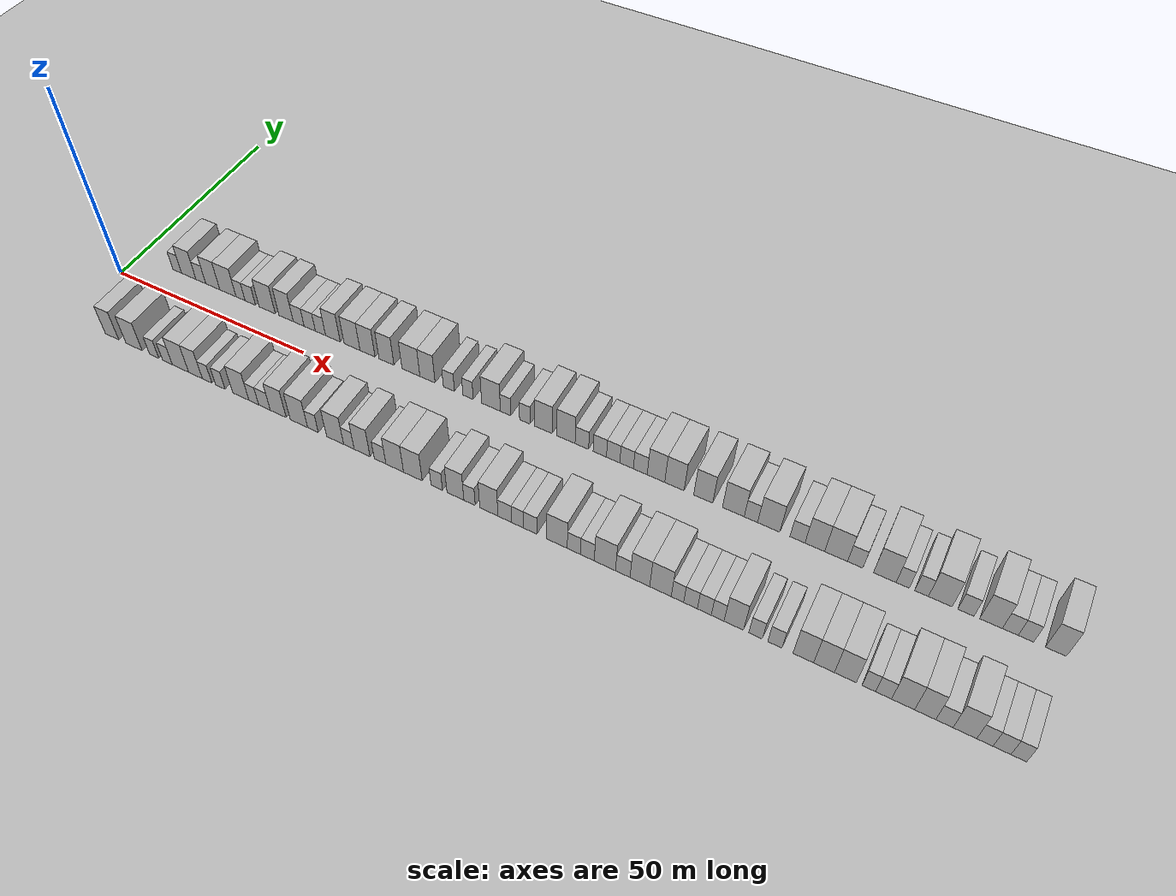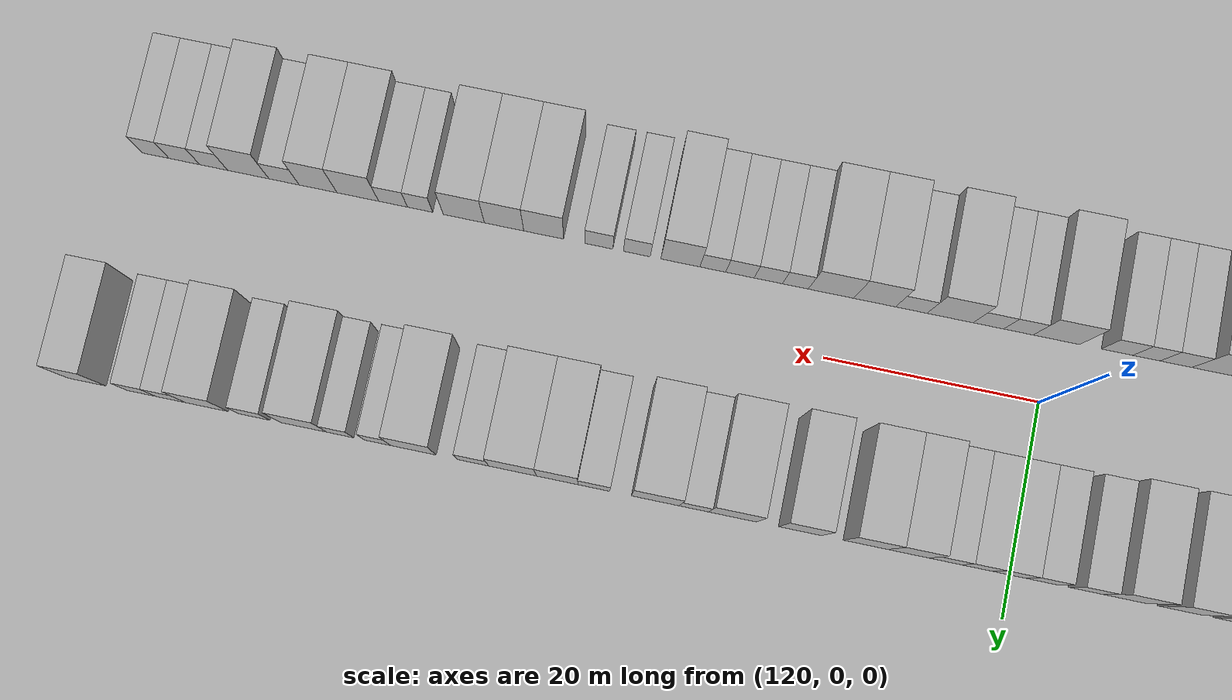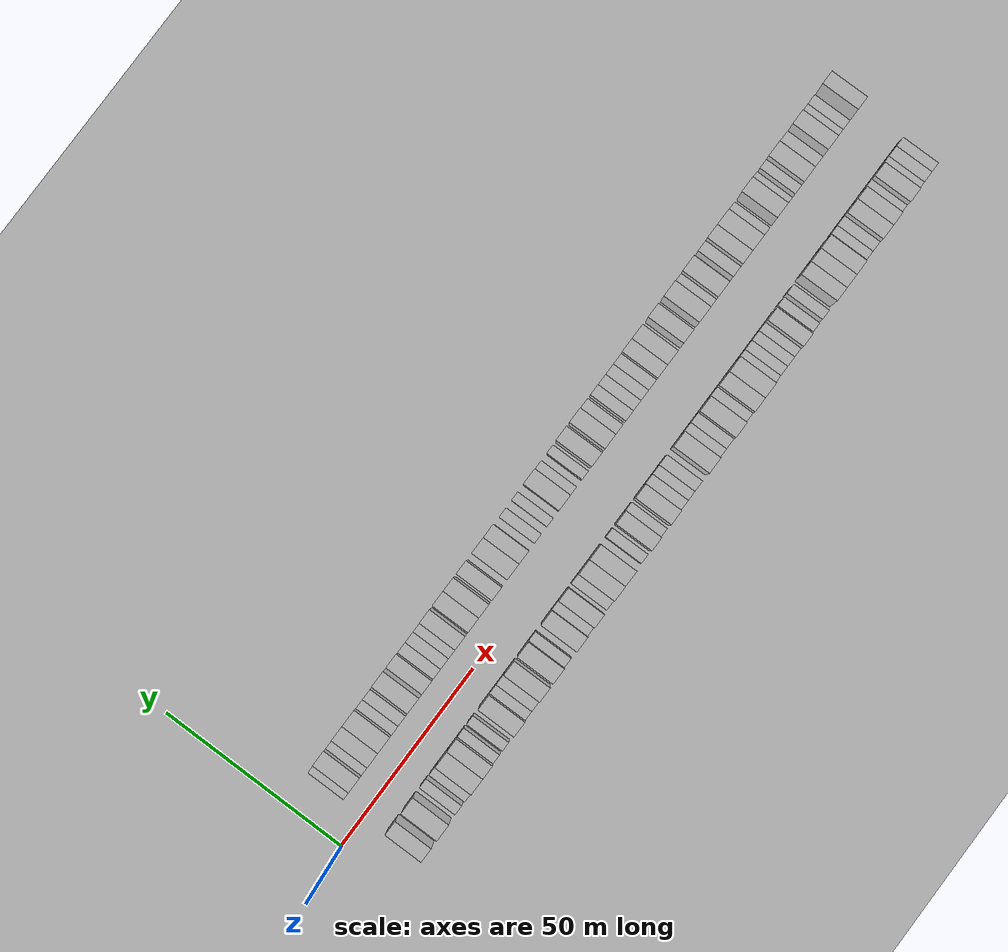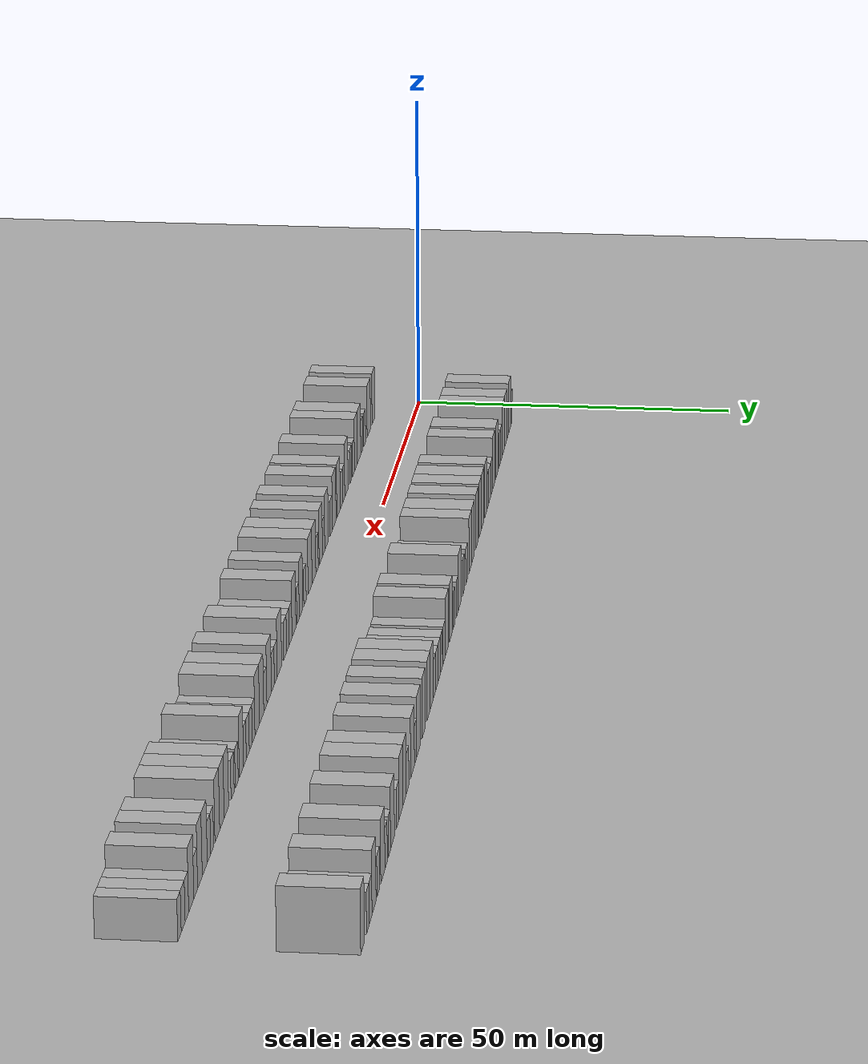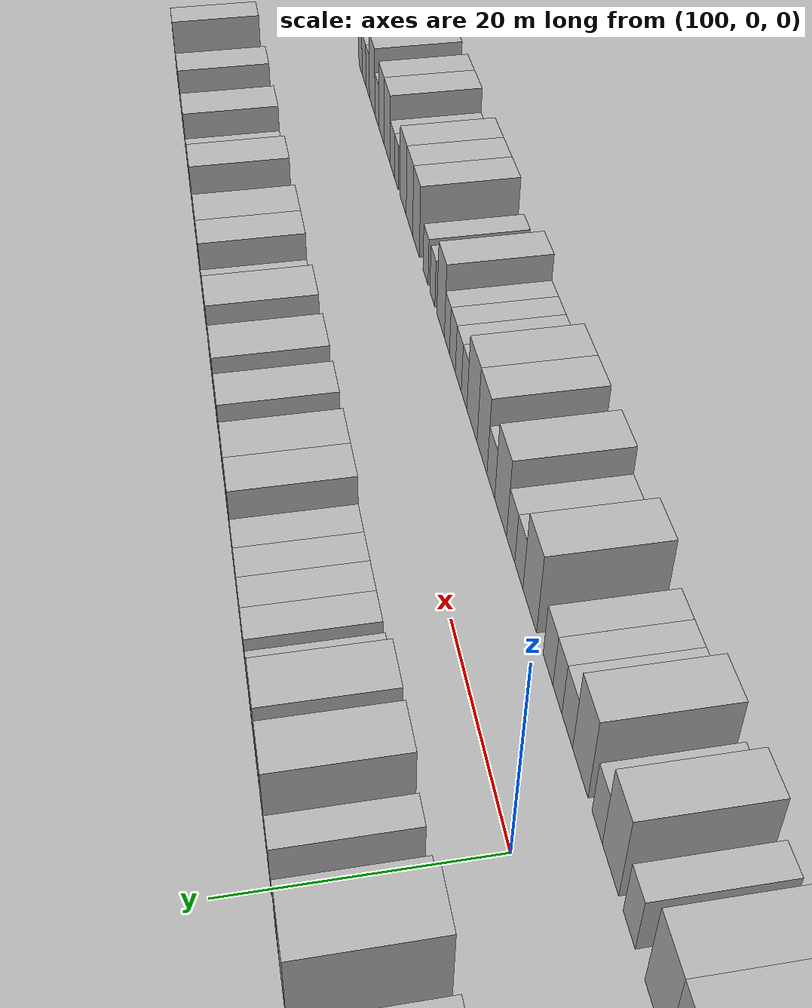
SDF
<?xml version="1.0" encoding="utf-8"?>

<sdf version="1.6">

   <world name="default">

      <gui fullscreen="0">

         <camera name="user_camera">

            <pose>-15 0 4.57585 0 0 0</pose>

            <view_controller>orbit</view_controller>

         </camera>

      </gui>

      <scene>

         <sky>

           <clouds>

             <speed>12</speed>

           </clouds>

         </sky>

         <ambient>0.4 0.4 0.4 1</ambient>

         <background>0.7 0.7 0.7 1</background>

         <shadows>1</shadows>

      </scene>

      <gravity>0 0 -9.8066</gravity>

      <magnetic_field>6e-06 2.3e-05 -4.2e-05</magnetic_field>

      <physics default="0" name="default_physics" type="ode">

         <ode>

            <solver>

               <type>quick</type>

               <iters>10</iters>

               <sor>1.0</sor>

               <use_dynamic_moi_rescaling>0</use_dynamic_moi_rescaling>

            </solver>

            <constraints>

               <cfm>0</cfm>

               <erp>0.2</erp>

               <contact_max_correcting_vel>100</contact_max_correcting_vel>

               <contact_surface_layer>0.001</contact_surface_layer>

            </constraints>

         </ode>

         <max_step_size>0.004</max_step_size>

         <real_time_factor>1</real_time_factor>

         <real_time_update_rate>250</real_time_update_rate>

      </physics>

      <light name="sun" type="directional">

         <cast_shadows>1</cast_shadows>

         <pose>0 0 10 0 0 0</pose>

         <diffuse>0.8 0.8 0.8 1</diffuse>

         <specular>0.2 0.2 0.2 1</specular>

         <attenuation>

            <range>1000</range>

            <constant>0.9</constant>

            <linear>0.01</linear>

            <quadratic>0.001</quadratic>

         </attenuation>

         <direction>-0.5 0.1 -0.9</direction>

      </light>

      <include>

         <name>ground_plane_1</name>

         <uri>model://HANNAS_ground_plane</uri>

         <pose>0 0 0  0 0 0</pose>

      </include>

      <include>

         <name>ground_plane_2</name>

         <uri>model://HANNAS_ground_plane</uri>

         <pose>100 0 0  0 0 0</pose>

      </include>

      <model name="building_1">

         <static>1</static>

         <pose frame="">11.2552 11.0000 0 0.000000 0.000000 1.570796</pose>

         <link name="link">

            <pose frame="">0 0 3.00 0 0 0</pose>

            <collision name="collision">

               <geometry>

                  <box>

                     <size>10.0000 2.5103 6.0000</size>

                  </box>

               </geometry>

               <max_contacts>10</max_contacts>

               <surface>

                  <contact>

                     <ode/>

                  </contact>

                  <bounce/>

                  <friction>

                     <torsional>

                        <ode/>

                     </torsional>

                     <ode/>

                  </friction>

               </surface>

            </collision>

            <visual name="visual">

               <cast_shadows>0</cast_shadows>

               <geometry>

                  <box>

                     <size>10.0000 2.5103 6.0000</size>

                  </box>

               </geometry>

               <material>

                  <script>

                     <uri>model://HANNAS_wall/materials/scripts</uri>

                     <uri>model://HANNAS_wall/materials/textures</uri>

                     <name>vrc/HANNAS_wall</name>

                  </script>

               </material>

            </visual>

            <self_collide>0</self_collide>

            <enable_wind>0</enable_wind>

            <kinematic>0</kinematic>

         </link>

      </model>

      <model name="building_2">

         <static>1</static>

         <pose frame="">14.5496 11.0000 0 0.000000 0.000000 1.570796</pose>

         <link name="link">

            <pose frame="">0 0 4.50 0 0 0</pose>

            <collision name="collision">

               <geometry>

                  <box>

                     <size>10.0000 4.0786 9.0000</size>

                  </box>

               </geometry>

               <max_contacts>10</max_contacts>

               <surface>

                  <contact>

                     <ode/>

                  </contact>

                  <bounce/>

                  <friction>

                     <torsional>

                        <ode/>

                     </torsional>

                     <ode/>

                  </friction>

               </surface>

            </collision>

            <visual name="visual">

               <cast_shadows>0</cast_shadows>

               <geometry>

                  <box>

                     <size>10.0000 4.0786 9.0000</size>

                  </box>

               </geometry>

               <material>

                  <script>

                     <uri>model://HANNAS_wall/materials/scripts</uri>

                     <uri>model://HANNAS_wall/materials/textures</uri>

                     <name>vrc/HANNAS_wall</name>

                  </script>

               </material>

            </visual>

            <self_collide>0</self_collide>

            <enable_wind>0</enable_wind>

            <kinematic>0</kinematic>

         </link>

      </model>

      <model name="building_3">

         <static>1</static>

         <pose frame="">17.9715 11.0000 0 0.000000 0.000000 1.570796</pose>

         <link name="link">

            <pose frame="">0 0 3.00 0 0 0</pose>

            <collision name="collision">

               <geometry>

                  <box>

                     <size>10.0000 2.7652 6.0000</size>

                  </box>

               </geometry>

               <max_contacts>10</max_contacts>

               <surface>

                  <contact>

                     <ode/>

                  </contact>

                  <bounce/>

                  <friction>

                     <torsional>

                        <ode/>

                     </torsional>

                     <ode/>

                  </friction>

               </surface>

            </collision>

            <visual name="visual">

               <cast_shadows>0</cast_shadows>

               <geometry>

                  <box>

                     <size>10.0000 2.7652 6.0000</size>

                  </box>

               </geometry>

               <material>

                  <script>

                     <uri>model://HANNAS_wall/materials/scripts</uri>

                     <uri>model://HANNAS_wall/materials/textures</uri>

                     <name>vrc/HANNAS_wall</name>

                  </script>

               </material>

            </visual>

            <self_collide>0</self_collide>

            <enable_wind>0</enable_wind>

            <kinematic>0</kinematic>

         </link>

      </model>

      <model name="building_4">

         <static>1</static>

         <pose frame="">21.3193 11.0000 0 0.000000 0.000000 1.570796</pose>

         <link name="link">

            <pose frame="">0 0 4.50 0 0 0</pose>

            <collision name="collision">

               <geometry>

                  <box>

                     <size>10.0000 3.9303 9.0000</size>

                  </box>

               </geometry>

               <max_contacts>10</max_contacts>

               <surface>

                  <contact>

                     <ode/>

                  </contact>

                  <bounce/>

                  <friction>

                     <torsional>

                        <ode/>

                     </torsional>

                     <ode/>

                  </friction>

               </surface>

            </collision>

            <visual name="visual">

               <cast_shadows>0</cast_shadows>

               <geometry>

                  <box>

                     <size>10.0000 3.9303 9.0000</size>

                  </box>

               </geometry>

               <material>

                  <script>

                     <uri>model://HANNAS_wall/materials/scripts</uri>

                     <uri>model://HANNAS_wall/materials/textures</uri>

                     <name>vrc/HANNAS_wall</name>

                  </script>

               </material>

            </visual>

            <self_collide>0</self_collide>

            <enable_wind>0</enable_wind>

            <kinematic>0</kinematic>

         </link>

      </model>

      <model name="building_5">

         <static>1</static>

         <pose frame="">25.5266 11.0000 0 0.000000 0.000000 1.570796</pose>

         <link name="link">

            <pose frame="">0 0 4.50 0 0 0</pose>

            <collision name="collision">

               <geometry>

                  <box>

                     <size>10.0000 4.4843 9.0000</size>

                  </box>

               </geometry>

               <max_contacts>10</max_contacts>

               <surface>

                  <contact>

                     <ode/>

                  </contact>

                  <bounce/>

                  <friction>

                     <torsional>

                        <ode/>

                     </torsional>

                     <ode/>

                  </friction>

               </surface>

            </collision>

            <visual name="visual">

               <cast_shadows>0</cast_shadows>

               <geometry>

                  <box>

                     <size>10.0000 4.4843 9.0000</size>

                  </box>

               </geometry>

               <material>

                  <script>

                     <uri>model://HANNAS_wall/materials/scripts</uri>

                     <uri>model://HANNAS_wall/materials/textures</uri>

                     <name>vrc/HANNAS_wall</name>

                  </script>

               </material>

            </visual>

            <self_collide>0</self_collide>

            <enable_wind>0</enable_wind>

            <kinematic>0</kinematic>

         </link>

      </model>

      <model name="building_6">

         <static>1</static>

         <pose frame="">29.0020 11.0000 0 0.000000 0.000000 1.570796</pose>

         <link name="link">

            <pose frame="">0 0 3.00 0 0 0</pose>

            <collision name="collision">

               <geometry>

                  <box>

                     <size>10.0000 2.4665 6.0000</size>

                  </box>

               </geometry>

               <max_contacts>10</max_contacts>

               <surface>

                  <contact>

                     <ode/>

                  </contact>

                  <bounce/>

                  <friction>

                     <torsional>

                        <ode/>

                     </torsional>

                     <ode/>

                  </friction>

               </surface>

            </collision>

            <visual name="visual">

               <cast_shadows>0</cast_shadows>

               <geometry>

                  <box>

                     <size>10.0000 2.4665 6.0000</size>

                  </box>

               </geometry>

               <material>

                  <script>

                     <uri>model://HANNAS_wall/materials/scripts</uri>

                     <uri>model://HANNAS_wall/materials/textures</uri>

                     <name>vrc/HANNAS_wall</name>

                  </script>

               </material>

            </visual>

            <self_collide>0</self_collide>

            <enable_wind>0</enable_wind>

            <kinematic>0</kinematic>

         </link>

      </model>

      <model name="building_7">

         <static>1</static>

         <pose frame="">31.6663 11.0000 0 0.000000 0.000000 1.570796</pose>

         <link name="link">

            <pose frame="">0 0 3.00 0 0 0</pose>

            <collision name="collision">

               <geometry>

                  <box>

                     <size>10.0000 2.8623 6.0000</size>

                  </box>

               </geometry>

               <max_contacts>10</max_contacts>

               <surface>

                  <contact>

                     <ode/>

                  </contact>

                  <bounce/>

                  <friction>

                     <torsional>

                        <ode/>

                     </torsional>

                     <ode/>

                  </friction>

               </surface>

            </collision>

            <visual name="visual">

               <cast_shadows>0</cast_shadows>

               <geometry>

                  <box>

                     <size>10.0000 2.8623 6.0000</size>

                  </box>

               </geometry>

               <material>

                  <script>

                     <uri>model://HANNAS_wall/materials/scripts</uri>

                     <uri>model://HANNAS_wall/materials/textures</uri>

                     <name>vrc/HANNAS_wall</name>

                  </script>

               </material>

            </visual>

            <self_collide>0</self_collide>

            <enable_wind>0</enable_wind>

            <kinematic>0</kinematic>

         </link>

      </model>

      <model name="building_8">

         <static>1</static>

         <pose frame="">36.2682 11.0000 0 0.000000 0.000000 1.570796</pose>

         <link name="link">

            <pose frame="">0 0 4.50 0 0 0</pose>

            <collision name="collision">

               <geometry>

                  <box>

                     <size>10.0000 4.3416 9.0000</size>

                  </box>

               </geometry>

               <max_contacts>10</max_contacts>

               <surface>

                  <contact>

                     <ode/>

                  </contact>

                  <bounce/>

                  <friction>

                     <torsional>

                        <ode/>

                     </torsional>

                     <ode/>

                  </friction>

               </surface>

            </collision>

            <visual name="visual">

               <cast_shadows>0</cast_shadows>

               <geometry>

                  <box>

                     <size>10.0000 4.3416 9.0000</size>

                  </box>

               </geometry>

               <material>

                  <script>

                     <uri>model://HANNAS_wall/materials/scripts</uri>

                     <uri>model://HANNAS_wall/materials/textures</uri>

                     <name>vrc/HANNAS_wall</name>

                  </script>

               </material>

            </visual>

            <self_collide>0</self_collide>

            <enable_wind>0</enable_wind>

            <kinematic>0</kinematic>

         </link>

      </model>

      <model name="building_9">

         <static>1</static>

         <pose frame="">41.3405 11.0000 0 0.000000 0.000000 1.570796</pose>

         <link name="link">

            <pose frame="">0 0 4.50 0 0 0</pose>

            <collision name="collision">

               <geometry>

                  <box>

                     <size>10.0000 3.8029 9.0000</size>

                  </box>

               </geometry>

               <max_contacts>10</max_contacts>

               <surface>

                  <contact>

                     <ode/>

                  </contact>

                  <bounce/>

                  <friction>

                     <torsional>

                        <ode/>

                     </torsional>

                     <ode/>

                  </friction>

               </surface>

            </collision>

            <visual name="visual">

               <cast_shadows>0</cast_shadows>

               <geometry>

                  <box>

                     <size>10.0000 3.8029 9.0000</size>

                  </box>

               </geometry>

               <material>

                  <script>

                     <uri>model://HANNAS_wall/materials/scripts</uri>

                     <uri>model://HANNAS_wall/materials/textures</uri>

                     <name>vrc/HANNAS_wall</name>

                  </script>

               </material>

            </visual>

            <self_collide>0</self_collide>

            <enable_wind>0</enable_wind>

            <kinematic>0</kinematic>

         </link>

      </model>

      <model name="building_10">

         <static>1</static>

         <pose frame="">44.6761 11.0000 0 0.000000 0.000000 1.570796</pose>

         <link name="link">

            <pose frame="">0 0 3.00 0 0 0</pose>

            <collision name="collision">

               <geometry>

                  <box>

                     <size>10.0000 2.8684 6.0000</size>

                  </box>

               </geometry>

               <max_contacts>10</max_contacts>

               <surface>

                  <contact>

                     <ode/>

                  </contact>

                  <bounce/>

                  <friction>

                     <torsional>

                        <ode/>

                     </torsional>

                     <ode/>

                  </friction>

               </surface>

            </collision>

            <visual name="visual">

               <cast_shadows>0</cast_shadows>

               <geometry>

                  <box>

                     <size>10.0000 2.8684 6.0000</size>

                  </box>

               </geometry>

               <material>

                  <script>

                     <uri>model://HANNAS_wall/materials/scripts</uri>

                     <uri>model://HANNAS_wall/materials/textures</uri>

                     <name>vrc/HANNAS_wall</name>

                  </script>

               </material>

            </visual>

            <self_collide>0</self_collide>

            <enable_wind>0</enable_wind>

            <kinematic>0</kinematic>

         </link>

      </model>

      <model name="building_11">

         <static>1</static>

         <pose frame="">47.5871 11.0000 0 0.000000 0.000000 1.570796</pose>

         <link name="link">

            <pose frame="">0 0 3.00 0 0 0</pose>

            <collision name="collision">

               <geometry>

                  <box>

                     <size>10.0000 2.9535 6.0000</size>

                  </box>

               </geometry>

               <max_contacts>10</max_contacts>

               <surface>

                  <contact>

                     <ode/>

                  </contact>

                  <bounce/>

                  <friction>

                     <torsional>

                        <ode/>

                     </torsional>

                     <ode/>

                  </friction>

               </surface>

            </collision>

            <visual name="visual">

               <cast_shadows>0</cast_shadows>

               <geometry>

                  <box>

                     <size>10.0000 2.9535 6.0000</size>

                  </box>

               </geometry>

               <material>

                  <script>

                     <uri>model://HANNAS_wall/materials/scripts</uri>

                     <uri>model://HANNAS_wall/materials/textures</uri>

                     <name>vrc/HANNAS_wall</name>

                  </script>

               </material>

            </visual>

            <self_collide>0</self_collide>

            <enable_wind>0</enable_wind>

            <kinematic>0</kinematic>

         </link>

      </model>

      <model name="building_12">

         <static>1</static>

         <pose frame="">50.3958 11.0000 0 0.000000 0.000000 1.570796</pose>

         <link name="link">

            <pose frame="">0 0 3.00 0 0 0</pose>

            <collision name="collision">

               <geometry>

                  <box>

                     <size>10.0000 2.6639 6.0000</size>

                  </box>

               </geometry>

               <max_contacts>10</max_contacts>

               <surface>

                  <contact>

                     <ode/>

                  </contact>

                  <bounce/>

                  <friction>

                     <torsional>

                        <ode/>

                     </torsional>

                     <ode/>

                  </friction>

               </surface>

            </collision>

            <visual name="visual">

               <cast_shadows>0</cast_shadows>

               <geometry>

                  <box>

                     <size>10.0000 2.6639 6.0000</size>

                  </box>

               </geometry>

               <material>

                  <script>

                     <uri>model://HANNAS_wall/materials/scripts</uri>

                     <uri>model://HANNAS_wall/materials/textures</uri>

                     <name>vrc/HANNAS_wall</name>

                  </script>

               </material>

            </visual>

            <self_collide>0</self_collide>

            <enable_wind>0</enable_wind>

            <kinematic>0</kinematic>

         </link>

      </model>

      <model name="building_13">

         <static>1</static>

         <pose frame="">53.6250 11.0000 0 0.000000 0.000000 1.570796</pose>

         <link name="link">

            <pose frame="">0 0 4.50 0 0 0</pose>

            <collision name="collision">

               <geometry>

                  <box>

                     <size>10.0000 3.7947 9.0000</size>

                  </box>

               </geometry>

               <max_contacts>10</max_contacts>

               <surface>

                  <contact>

                     <ode/>

                  </contact>

                  <bounce/>

                  <friction>

                     <torsional>

                        <ode/>

                     </torsional>

                     <ode/>

                  </friction>

               </surface>

            </collision>

            <visual name="visual">

               <cast_shadows>0</cast_shadows>

               <geometry>

                  <box>

                     <size>10.0000 3.7947 9.0000</size>

                  </box>

               </geometry>

               <material>

                  <script>

                     <uri>model://HANNAS_wall/materials/scripts</uri>

                     <uri>model://HANNAS_wall/materials/textures</uri>

                     <name>vrc/HANNAS_wall</name>

                  </script>

               </material>

            </visual>

            <self_collide>0</self_collide>

            <enable_wind>0</enable_wind>

            <kinematic>0</kinematic>

         </link>

      </model>

      <model name="building_14">

         <static>1</static>

         <pose frame="">58.5556 11.0000 0 0.000000 0.000000 1.570796</pose>

         <link name="link">

            <pose frame="">0 0 4.50 0 0 0</pose>

            <collision name="collision">

               <geometry>

                  <box>

                     <size>10.0000 4.0664 9.0000</size>

                  </box>

               </geometry>

               <max_contacts>10</max_contacts>

               <surface>

                  <contact>

                     <ode/>

                  </contact>

                  <bounce/>

                  <friction>

                     <torsional>

                        <ode/>

                     </torsional>

                     <ode/>

                  </friction>

               </surface>

            </collision>

            <visual name="visual">

               <cast_shadows>0</cast_shadows>

               <geometry>

                  <box>

                     <size>10.0000 4.0664 9.0000</size>

                  </box>

               </geometry>

               <material>

                  <script>

                     <uri>model://HANNAS_wall/materials/scripts</uri>

                     <uri>model://HANNAS_wall/materials/textures</uri>

                     <name>vrc/HANNAS_wall</name>

                  </script>

               </material>

            </visual>

            <self_collide>0</self_collide>

            <enable_wind>0</enable_wind>

            <kinematic>0</kinematic>

         </link>

      </model>

      <model name="building_15">

         <static>1</static>

         <pose frame="">62.4908 11.0000 0 0.000000 0.000000 1.570796</pose>

         <link name="link">

            <pose frame="">0 0 4.50 0 0 0</pose>

            <collision name="collision">

               <geometry>

                  <box>

                     <size>10.0000 3.8040 9.0000</size>

                  </box>

               </geometry>

               <max_contacts>10</max_contacts>

               <surface>

                  <contact>

                     <ode/>

                  </contact>

                  <bounce/>

                  <friction>

                     <torsional>

                        <ode/>

                     </torsional>

                     <ode/>

                  </friction>

               </surface>

            </collision>

            <visual name="visual">

               <cast_shadows>0</cast_shadows>

               <geometry>

                  <box>

                     <size>10.0000 3.8040 9.0000</size>

                  </box>

               </geometry>

               <material>

                  <script>

                     <uri>model://HANNAS_wall/materials/scripts</uri>

                     <uri>model://HANNAS_wall/materials/textures</uri>

                     <name>vrc/HANNAS_wall</name>

                  </script>

               </material>

            </visual>

            <self_collide>0</self_collide>

            <enable_wind>0</enable_wind>

            <kinematic>0</kinematic>

         </link>

      </model>

      <model name="building_16">

         <static>1</static>

         <pose frame="">67.2608 11.0000 0 0.000000 0.000000 1.570796</pose>

         <link name="link">

            <pose frame="">0 0 4.50 0 0 0</pose>

            <collision name="collision">

               <geometry>

                  <box>

                     <size>10.0000 3.7361 9.0000</size>

                  </box>

               </geometry>

               <max_contacts>10</max_contacts>

               <surface>

                  <contact>

                     <ode/>

                  </contact>

                  <bounce/>

                  <friction>

                     <torsional>

                        <ode/>

                     </torsional>

                     <ode/>

                  </friction>

               </surface>

            </collision>

            <visual name="visual">

               <cast_shadows>0</cast_shadows>

               <geometry>

                  <box>

                     <size>10.0000 3.7361 9.0000</size>

                  </box>

               </geometry>

               <material>

                  <script>

                     <uri>model://HANNAS_wall/materials/scripts</uri>

                     <uri>model://HANNAS_wall/materials/textures</uri>

                     <name>vrc/HANNAS_wall</name>

                  </script>

               </material>

            </visual>

            <self_collide>0</self_collide>

            <enable_wind>0</enable_wind>

            <kinematic>0</kinematic>

         </link>

      </model>

      <model name="building_17">

         <static>1</static>

         <pose frame="">73.3346 11.0000 0 0.000000 0.000000 1.570796</pose>

         <link name="link">

            <pose frame="">0 0 4.50 0 0 0</pose>

            <collision name="collision">

               <geometry>

                  <box>

                     <size>10.0000 4.4116 9.0000</size>

                  </box>

               </geometry>

               <max_contacts>10</max_contacts>

               <surface>

                  <contact>

                     <ode/>

                  </contact>

                  <bounce/>

                  <friction>

                     <torsional>

                        <ode/>

                     </torsional>

                     <ode/>

                  </friction>

               </surface>

            </collision>

            <visual name="visual">

               <cast_shadows>0</cast_shadows>

               <geometry>

                  <box>

                     <size>10.0000 4.4116 9.0000</size>

                  </box>

               </geometry>

               <material>

                  <script>

                     <uri>model://HANNAS_wall/materials/scripts</uri>

                     <uri>model://HANNAS_wall/materials/textures</uri>

                     <name>vrc/HANNAS_wall</name>

                  </script>

               </material>

            </visual>

            <self_collide>0</self_collide>

            <enable_wind>0</enable_wind>

            <kinematic>0</kinematic>

         </link>

      </model>

      <model name="building_18">

         <static>1</static>

         <pose frame="">77.3870 11.0000 0 0.000000 0.000000 1.570796</pose>

         <link name="link">

            <pose frame="">0 0 4.50 0 0 0</pose>

            <collision name="collision">

               <geometry>

                  <box>

                     <size>10.0000 3.6932 9.0000</size>

                  </box>

               </geometry>

               <max_contacts>10</max_contacts>

               <surface>

                  <contact>

                     <ode/>

                  </contact>

                  <bounce/>

                  <friction>

                     <torsional>

                        <ode/>

                     </torsional>

                     <ode/>

                  </friction>

               </surface>

            </collision>

            <visual name="visual">

               <cast_shadows>0</cast_shadows>

               <geometry>

                  <box>

                     <size>10.0000 3.6932 9.0000</size>

                  </box>

               </geometry>

               <material>

                  <script>

                     <uri>model://HANNAS_wall/materials/scripts</uri>

                     <uri>model://HANNAS_wall/materials/textures</uri>

                     <name>vrc/HANNAS_wall</name>

                  </script>

               </material>

            </visual>

            <self_collide>0</self_collide>

            <enable_wind>0</enable_wind>

            <kinematic>0</kinematic>

         </link>

      </model>

      <model name="building_19">

         <static>1</static>

         <pose frame="">82.5772 11.0000 0 0.000000 0.000000 1.570796</pose>

         <link name="link">

            <pose frame="">0 0 3.00 0 0 0</pose>

            <collision name="collision">

               <geometry>

                  <box>

                     <size>10.0000 2.6872 6.0000</size>

                  </box>

               </geometry>

               <max_contacts>10</max_contacts>

               <surface>

                  <contact>

                     <ode/>

                  </contact>

                  <bounce/>

                  <friction>

                     <torsional>

                        <ode/>

                     </torsional>

                     <ode/>

                  </friction>

               </surface>

            </collision>

            <visual name="visual">

               <cast_shadows>0</cast_shadows>

               <geometry>

                  <box>

                     <size>10.0000 2.6872 6.0000</size>

                  </box>

               </geometry>

               <material>

                  <script>

                     <uri>model://HANNAS_wall/materials/scripts</uri>

                     <uri>model://HANNAS_wall/materials/textures</uri>

                     <name>vrc/HANNAS_wall</name>

                  </script>

               </material>

            </visual>

            <self_collide>0</self_collide>

            <enable_wind>0</enable_wind>

            <kinematic>0</kinematic>

         </link>

      </model>

      <model name="building_20">

         <static>1</static>

         <pose frame="">87.1497 11.0000 0 0.000000 0.000000 1.570796</pose>

         <link name="link">

            <pose frame="">0 0 3.00 0 0 0</pose>

            <collision name="collision">

               <geometry>

                  <box>

                     <size>10.0000 2.4577 6.0000</size>

                  </box>

               </geometry>

               <max_contacts>10</max_contacts>

               <surface>

                  <contact>

                     <ode/>

                  </contact>

                  <bounce/>

                  <friction>

                     <torsional>

                        <ode/>

                     </torsional>

                     <ode/>

                  </friction>

               </surface>

            </collision>

            <visual name="visual">

               <cast_shadows>0</cast_shadows>

               <geometry>

                  <box>

                     <size>10.0000 2.4577 6.0000</size>

                  </box>

               </geometry>

               <material>

                  <script>

                     <uri>model://HANNAS_wall/materials/scripts</uri>

                     <uri>model://HANNAS_wall/materials/textures</uri>

                     <name>vrc/HANNAS_wall</name>

                  </script>

               </material>

            </visual>

            <self_collide>0</self_collide>

            <enable_wind>0</enable_wind>

            <kinematic>0</kinematic>

         </link>

      </model>

      <model name="building_21">

         <static>1</static>

         <pose frame="">92.5695 11.0000 0 0.000000 0.000000 1.570796</pose>

         <link name="link">

            <pose frame="">0 0 4.50 0 0 0</pose>

            <collision name="collision">

               <geometry>

                  <box>

                     <size>10.0000 4.3818 9.0000</size>

                  </box>

               </geometry>

               <max_contacts>10</max_contacts>

               <surface>

                  <contact>

                     <ode/>

                  </contact>

                  <bounce/>

                  <friction>

                     <torsional>

                        <ode/>

                     </torsional>

                     <ode/>

                  </friction>

               </surface>

            </collision>

            <visual name="visual">

               <cast_shadows>0</cast_shadows>

               <geometry>

                  <box>

                     <size>10.0000 4.3818 9.0000</size>

                  </box>

               </geometry>

               <material>

                  <script>

                     <uri>model://HANNAS_wall/materials/scripts</uri>

                     <uri>model://HANNAS_wall/materials/textures</uri>

                     <name>vrc/HANNAS_wall</name>

                  </script>

               </material>

            </visual>

            <self_collide>0</self_collide>

            <enable_wind>0</enable_wind>

            <kinematic>0</kinematic>

         </link>

      </model>

      <model name="building_22">

         <static>1</static>

         <pose frame="">95.9836 11.0000 0 0.000000 0.000000 1.570796</pose>

         <link name="link">

            <pose frame="">0 0 3.00 0 0 0</pose>

            <collision name="collision">

               <geometry>

                  <box>

                     <size>10.0000 2.4465 6.0000</size>

                  </box>

               </geometry>

               <max_contacts>10</max_contacts>

               <surface>

                  <contact>

                     <ode/>

                  </contact>

                  <bounce/>

                  <friction>

                     <torsional>

                        <ode/>

                     </torsional>

                     <ode/>

                  </friction>

               </surface>

            </collision>

            <visual name="visual">

               <cast_shadows>0</cast_shadows>

               <geometry>

                  <box>

                     <size>10.0000 2.4465 6.0000</size>

                  </box>

               </geometry>

               <material>

                  <script>

                     <uri>model://HANNAS_wall/materials/scripts</uri>

                     <uri>model://HANNAS_wall/materials/textures</uri>

                     <name>vrc/HANNAS_wall</name>

                  </script>

               </material>

            </visual>

            <self_collide>0</self_collide>

            <enable_wind>0</enable_wind>

            <kinematic>0</kinematic>

         </link>

      </model>

      <model name="building_23">

         <static>1</static>

         <pose frame="">100.4280 11.0000 0 0.000000 0.000000 1.570796</pose>

         <link name="link">

            <pose frame="">0 0 3.00 0 0 0</pose>

            <collision name="collision">

               <geometry>

                  <box>

                     <size>10.0000 2.4423 6.0000</size>

                  </box>

               </geometry>

               <max_contacts>10</max_contacts>

               <surface>

                  <contact>

                     <ode/>

                  </contact>

                  <bounce/>

                  <friction>

                     <torsional>

                        <ode/>

                     </torsional>

                     <ode/>

                  </friction>

               </surface>

            </collision>

            <visual name="visual">

               <cast_shadows>0</cast_shadows>

               <geometry>

                  <box>

                     <size>10.0000 2.4423 6.0000</size>

                  </box>

               </geometry>

               <material>

                  <script>

                     <uri>model://HANNAS_wall/materials/scripts</uri>

                     <uri>model://HANNAS_wall/materials/textures</uri>

                     <name>vrc/HANNAS_wall</name>

                  </script>

               </material>

            </visual>

            <self_collide>0</self_collide>

            <enable_wind>0</enable_wind>

            <kinematic>0</kinematic>

         </link>

      </model>

      <model name="building_24">

         <static>1</static>

         <pose frame="">104.6647 11.0000 0 0.000000 0.000000 1.570796</pose>

         <link name="link">

            <pose frame="">0 0 4.50 0 0 0</pose>

            <collision name="collision">

               <geometry>

                  <box>

                     <size>10.0000 4.0310 9.0000</size>

                  </box>

               </geometry>

               <max_contacts>10</max_contacts>

               <surface>

                  <contact>

                     <ode/>

                  </contact>

                  <bounce/>

                  <friction>

                     <torsional>

                        <ode/>

                     </torsional>

                     <ode/>

                  </friction>

               </surface>

            </collision>

            <visual name="visual">

               <cast_shadows>0</cast_shadows>

               <geometry>

                  <box>

                     <size>10.0000 4.0310 9.0000</size>

                  </box>

               </geometry>

               <material>

                  <script>

                     <uri>model://HANNAS_wall/materials/scripts</uri>

                     <uri>model://HANNAS_wall/materials/textures</uri>

                     <name>vrc/HANNAS_wall</name>

                  </script>

               </material>

            </visual>

            <self_collide>0</self_collide>

            <enable_wind>0</enable_wind>

            <kinematic>0</kinematic>

         </link>

      </model>

      <model name="building_25">

         <static>1</static>

         <pose frame="">109.7369 11.0000 0 0.000000 0.000000 1.570796</pose>

         <link name="link">

            <pose frame="">0 0 4.50 0 0 0</pose>

            <collision name="collision">

               <geometry>

                  <box>

                     <size>10.0000 4.1134 9.0000</size>

                  </box>

               </geometry>

               <max_contacts>10</max_contacts>

               <surface>

                  <contact>

                     <ode/>

                  </contact>

                  <bounce/>

                  <friction>

                     <torsional>

                        <ode/>

                     </torsional>

                     <ode/>

                  </friction>

               </surface>

            </collision>

            <visual name="visual">

               <cast_shadows>0</cast_shadows>

               <geometry>

                  <box>

                     <size>10.0000 4.1134 9.0000</size>

                  </box>

               </geometry>

               <material>

                  <script>

                     <uri>model://HANNAS_wall/materials/scripts</uri>

                     <uri>model://HANNAS_wall/materials/textures</uri>

                     <name>vrc/HANNAS_wall</name>

                  </script>

               </material>

            </visual>

            <self_collide>0</self_collide>

            <enable_wind>0</enable_wind>

            <kinematic>0</kinematic>

         </link>

      </model>

      <model name="building_26">

         <static>1</static>

         <pose frame="">113.2875 11.0000 0 0.000000 0.000000 1.570796</pose>

         <link name="link">

            <pose frame="">0 0 3.00 0 0 0</pose>

            <collision name="collision">

               <geometry>

                  <box>

                     <size>10.0000 2.9878 6.0000</size>

                  </box>

               </geometry>

               <max_contacts>10</max_contacts>

               <surface>

                  <contact>

                     <ode/>

                  </contact>

                  <bounce/>

                  <friction>

                     <torsional>

                        <ode/>

                     </torsional>

                     <ode/>

                  </friction>

               </surface>

            </collision>

            <visual name="visual">

               <cast_shadows>0</cast_shadows>

               <geometry>

                  <box>

                     <size>10.0000 2.9878 6.0000</size>

                  </box>

               </geometry>

               <material>

                  <script>

                     <uri>model://HANNAS_wall/materials/scripts</uri>

                     <uri>model://HANNAS_wall/materials/textures</uri>

                     <name>vrc/HANNAS_wall</name>

                  </script>

               </material>

            </visual>

            <self_collide>0</self_collide>

            <enable_wind>0</enable_wind>

            <kinematic>0</kinematic>

         </link>

      </model>

      <model name="building_27">

         <static>1</static>

         <pose frame="">117.2467 11.0000 0 0.000000 0.000000 1.570796</pose>

         <link name="link">

            <pose frame="">0 0 3.00 0 0 0</pose>

            <collision name="collision">

               <geometry>

                  <box>

                     <size>10.0000 2.9308 6.0000</size>

                  </box>

               </geometry>

               <max_contacts>10</max_contacts>

               <surface>

                  <contact>

                     <ode/>

                  </contact>

                  <bounce/>

                  <friction>

                     <torsional>

                        <ode/>

                     </torsional>

                     <ode/>

                  </friction>

               </surface>

            </collision>

            <visual name="visual">

               <cast_shadows>0</cast_shadows>

               <geometry>

                  <box>

                     <size>10.0000 2.9308 6.0000</size>

                  </box>

               </geometry>

               <material>

                  <script>

                     <uri>model://HANNAS_wall/materials/scripts</uri>

                     <uri>model://HANNAS_wall/materials/textures</uri>

                     <name>vrc/HANNAS_wall</name>

                  </script>

               </material>

            </visual>

            <self_collide>0</self_collide>

            <enable_wind>0</enable_wind>

            <kinematic>0</kinematic>

         </link>

      </model>

      <model name="building_28">

         <static>1</static>

         <pose frame="">120.1706 11.0000 0 0.000000 0.000000 1.570796</pose>

         <link name="link">

            <pose frame="">0 0 3.00 0 0 0</pose>

            <collision name="collision">

               <geometry>

                  <box>

                     <size>10.0000 2.9170 6.0000</size>

                  </box>

               </geometry>

               <max_contacts>10</max_contacts>

               <surface>

                  <contact>

                     <ode/>

                  </contact>

                  <bounce/>

                  <friction>

                     <torsional>

                        <ode/>

                     </torsional>

                     <ode/>

                  </friction>

               </surface>

            </collision>

            <visual name="visual">

               <cast_shadows>0</cast_shadows>

               <geometry>

                  <box>

                     <size>10.0000 2.9170 6.0000</size>

                  </box>

               </geometry>

               <material>

                  <script>

                     <uri>model://HANNAS_wall/materials/scripts</uri>

                     <uri>model://HANNAS_wall/materials/textures</uri>

                     <name>vrc/HANNAS_wall</name>

                  </script>

               </material>

            </visual>

            <self_collide>0</self_collide>

            <enable_wind>0</enable_wind>

            <kinematic>0</kinematic>

         </link>

      </model>

      <model name="building_29">

         <static>1</static>

         <pose frame="">123.0961 11.0000 0 0.000000 0.000000 1.570796</pose>

         <link name="link">

            <pose frame="">0 0 3.00 0 0 0</pose>

            <collision name="collision">

               <geometry>

                  <box>

                     <size>10.0000 2.9340 6.0000</size>

                  </box>

               </geometry>

               <max_contacts>10</max_contacts>

               <surface>

                  <contact>

                     <ode/>

                  </contact>

                  <bounce/>

                  <friction>

                     <torsional>

                        <ode/>

                     </torsional>

                     <ode/>

                  </friction>

               </surface>

            </collision>

            <visual name="visual">

               <cast_shadows>0</cast_shadows>

               <geometry>

                  <box>

                     <size>10.0000 2.9340 6.0000</size>

                  </box>

               </geometry>

               <material>

                  <script>

                     <uri>model://HANNAS_wall/materials/scripts</uri>

                     <uri>model://HANNAS_wall/materials/textures</uri>

                     <name>vrc/HANNAS_wall</name>

                  </script>

               </material>

            </visual>

            <self_collide>0</self_collide>

            <enable_wind>0</enable_wind>

            <kinematic>0</kinematic>

         </link>

      </model>

      <model name="building_30">

         <static>1</static>

         <pose frame="">126.0458 11.0000 0 0.000000 0.000000 1.570796</pose>

         <link name="link">

            <pose frame="">0 0 3.00 0 0 0</pose>

            <collision name="collision">

               <geometry>

                  <box>

                     <size>10.0000 2.9655 6.0000</size>

                  </box>

               </geometry>

               <max_contacts>10</max_contacts>

               <surface>

                  <contact>

                     <ode/>

                  </contact>

                  <bounce/>

                  <friction>

                     <torsional>

                        <ode/>

                     </torsional>

                     <ode/>

                  </friction>

               </surface>

            </collision>

            <visual name="visual">

               <cast_shadows>0</cast_shadows>

               <geometry>

                  <box>

                     <size>10.0000 2.9655 6.0000</size>

                  </box>

               </geometry>

               <material>

                  <script>

                     <uri>model://HANNAS_wall/materials/scripts</uri>

                     <uri>model://HANNAS_wall/materials/textures</uri>

                     <name>vrc/HANNAS_wall</name>

                  </script>

               </material>

            </visual>

            <self_collide>0</self_collide>

            <enable_wind>0</enable_wind>

            <kinematic>0</kinematic>

         </link>

      </model>

      <model name="building_31">

         <static>1</static>

         <pose frame="">129.3973 11.0000 0 0.000000 0.000000 1.570796</pose>

         <link name="link">

            <pose frame="">0 0 4.50 0 0 0</pose>

            <collision name="collision">

               <geometry>

                  <box>

                     <size>10.0000 3.7374 9.0000</size>

                  </box>

               </geometry>

               <max_contacts>10</max_contacts>

               <surface>

                  <contact>

                     <ode/>

                  </contact>

                  <bounce/>

                  <friction>

                     <torsional>

                        <ode/>

                     </torsional>

                     <ode/>

                  </friction>

               </surface>

            </collision>

            <visual name="visual">

               <cast_shadows>0</cast_shadows>

               <geometry>

                  <box>

                     <size>10.0000 3.7374 9.0000</size>

                  </box>

               </geometry>

               <material>

                  <script>

                     <uri>model://HANNAS_wall/materials/scripts</uri>

                     <uri>model://HANNAS_wall/materials/textures</uri>

                     <name>vrc/HANNAS_wall</name>

                  </script>

               </material>

            </visual>

            <self_collide>0</self_collide>

            <enable_wind>0</enable_wind>

            <kinematic>0</kinematic>

         </link>

      </model>

      <model name="building_32">

         <static>1</static>

         <pose frame="">133.3034 11.0000 0 0.000000 0.000000 1.570796</pose>

         <link name="link">

            <pose frame="">0 0 4.50 0 0 0</pose>

            <collision name="collision">

               <geometry>

                  <box>

                     <size>10.0000 4.0748 9.0000</size>

                  </box>

               </geometry>

               <max_contacts>10</max_contacts>

               <surface>

                  <contact>

                     <ode/>

                  </contact>

                  <bounce/>

                  <friction>

                     <torsional>

                        <ode/>

                     </torsional>

                     <ode/>

                  </friction>

               </surface>

            </collision>

            <visual name="visual">

               <cast_shadows>0</cast_shadows>

               <geometry>

                  <box>

                     <size>10.0000 4.0748 9.0000</size>

                  </box>

               </geometry>

               <material>

                  <script>

                     <uri>model://HANNAS_wall/materials/scripts</uri>

                     <uri>model://HANNAS_wall/materials/textures</uri>

                     <name>vrc/HANNAS_wall</name>

                  </script>

               </material>

            </visual>

            <self_collide>0</self_collide>

            <enable_wind>0</enable_wind>

            <kinematic>0</kinematic>

         </link>

      </model>

      <model name="building_33">

         <static>1</static>

         <pose frame="">139.3110 11.0000 0 0.000000 0.000000 1.570796</pose>

         <link name="link">

            <pose frame="">0 0 4.50 0 0 0</pose>

            <collision name="collision">

               <geometry>

                  <box>

                     <size>10.0000 3.9404 9.0000</size>

                  </box>

               </geometry>

               <max_contacts>10</max_contacts>

               <surface>

                  <contact>

                     <ode/>

                  </contact>

                  <bounce/>

                  <friction>

                     <torsional>

                        <ode/>

                     </torsional>

                     <ode/>

                  </friction>

               </surface>

            </collision>

            <visual name="visual">

               <cast_shadows>0</cast_shadows>

               <geometry>

                  <box>

                     <size>10.0000 3.9404 9.0000</size>

                  </box>

               </geometry>

               <material>

                  <script>

                     <uri>model://HANNAS_wall/materials/scripts</uri>

                     <uri>model://HANNAS_wall/materials/textures</uri>

                     <name>vrc/HANNAS_wall</name>

                  </script>

               </material>

            </visual>

            <self_collide>0</self_collide>

            <enable_wind>0</enable_wind>

            <kinematic>0</kinematic>

         </link>

      </model>

      <model name="building_34">

         <static>1</static>

         <pose frame="">145.5009 11.0000 0 0.000000 0.000000 1.570796</pose>

         <link name="link">

            <pose frame="">0 0 4.50 0 0 0</pose>

            <collision name="collision">

               <geometry>

                  <box>

                     <size>10.0000 4.4395 9.0000</size>

                  </box>

               </geometry>

               <max_contacts>10</max_contacts>

               <surface>

                  <contact>

                     <ode/>

                  </contact>

                  <bounce/>

                  <friction>

                     <torsional>

                        <ode/>

                     </torsional>

                     <ode/>

                  </friction>

               </surface>

            </collision>

            <visual name="visual">

               <cast_shadows>0</cast_shadows>

               <geometry>

                  <box>

                     <size>10.0000 4.4395 9.0000</size>

                  </box>

               </geometry>

               <material>

                  <script>

                     <uri>model://HANNAS_wall/materials/scripts</uri>

                     <uri>model://HANNAS_wall/materials/textures</uri>

                     <name>vrc/HANNAS_wall</name>

                  </script>

               </material>

            </visual>

            <self_collide>0</self_collide>

            <enable_wind>0</enable_wind>

            <kinematic>0</kinematic>

         </link>

      </model>

      <model name="building_35">

         <static>1</static>

         <pose frame="">149.0695 11.0000 0 0.000000 0.000000 1.570796</pose>

         <link name="link">

            <pose frame="">0 0 3.00 0 0 0</pose>

            <collision name="collision">

               <geometry>

                  <box>

                     <size>10.0000 2.6977 6.0000</size>

                  </box>

               </geometry>

               <max_contacts>10</max_contacts>

               <surface>

                  <contact>

                     <ode/>

                  </contact>

                  <bounce/>

                  <friction>

                     <torsional>

                        <ode/>

                     </torsional>

                     <ode/>

                  </friction>

               </surface>

            </collision>

            <visual name="visual">

               <cast_shadows>0</cast_shadows>

               <geometry>

                  <box>

                     <size>10.0000 2.6977 6.0000</size>

                  </box>

               </geometry>

               <material>

                  <script>

                     <uri>model://HANNAS_wall/materials/scripts</uri>

                     <uri>model://HANNAS_wall/materials/textures</uri>

                     <name>vrc/HANNAS_wall</name>

                  </script>

               </material>

            </visual>

            <self_collide>0</self_collide>

            <enable_wind>0</enable_wind>

            <kinematic>0</kinematic>

         </link>

      </model>

      <model name="building_36">

         <static>1</static>

         <pose frame="">152.6333 11.0000 0 0.000000 0.000000 1.570796</pose>

         <link name="link">

            <pose frame="">0 0 4.50 0 0 0</pose>

            <collision name="collision">

               <geometry>

                  <box>

                     <size>10.0000 4.4298 9.0000</size>

                  </box>

               </geometry>

               <max_contacts>10</max_contacts>

               <surface>

                  <contact>

                     <ode/>

                  </contact>

                  <bounce/>

                  <friction>

                     <torsional>

                        <ode/>

                     </torsional>

                     <ode/>

                  </friction>

               </surface>

            </collision>

            <visual name="visual">

               <cast_shadows>0</cast_shadows>

               <geometry>

                  <box>

                     <size>10.0000 4.4298 9.0000</size>

                  </box>

               </geometry>

               <material>

                  <script>

                     <uri>model://HANNAS_wall/materials/scripts</uri>

                     <uri>model://HANNAS_wall/materials/textures</uri>

                     <name>vrc/HANNAS_wall</name>

                  </script>

               </material>

            </visual>

            <self_collide>0</self_collide>

            <enable_wind>0</enable_wind>

            <kinematic>0</kinematic>

         </link>

      </model>

      <model name="building_37">

         <static>1</static>

         <pose frame="">158.3237 11.0000 0 0.000000 0.000000 1.570796</pose>

         <link name="link">

            <pose frame="">0 0 3.00 0 0 0</pose>

            <collision name="collision">

               <geometry>

                  <box>

                     <size>10.0000 2.9511 6.0000</size>

                  </box>

               </geometry>

               <max_contacts>10</max_contacts>

               <surface>

                  <contact>

                     <ode/>

                  </contact>

                  <bounce/>

                  <friction>

                     <torsional>

                        <ode/>

                     </torsional>

                     <ode/>

                  </friction>

               </surface>

            </collision>

            <visual name="visual">

               <cast_shadows>0</cast_shadows>

               <geometry>

                  <box>

                     <size>10.0000 2.9511 6.0000</size>

                  </box>

               </geometry>

               <material>

                  <script>

                     <uri>model://HANNAS_wall/materials/scripts</uri>

                     <uri>model://HANNAS_wall/materials/textures</uri>

                     <name>vrc/HANNAS_wall</name>

                  </script>

               </material>

            </visual>

            <self_collide>0</self_collide>

            <enable_wind>0</enable_wind>

            <kinematic>0</kinematic>

         </link>

      </model>

      <model name="building_38">

         <static>1</static>

         <pose frame="">161.7104 11.0000 0 0.000000 0.000000 1.570796</pose>

         <link name="link">

            <pose frame="">0 0 4.50 0 0 0</pose>

            <collision name="collision">

               <geometry>

                  <box>

                     <size>10.0000 3.8222 9.0000</size>

                  </box>

               </geometry>

               <max_contacts>10</max_contacts>

               <surface>

                  <contact>

                     <ode/>

                  </contact>

                  <bounce/>

                  <friction>

                     <torsional>

                        <ode/>

                     </torsional>

                     <ode/>

                  </friction>

               </surface>

            </collision>

            <visual name="visual">

               <cast_shadows>0</cast_shadows>

               <geometry>

                  <box>

                     <size>10.0000 3.8222 9.0000</size>

                  </box>

               </geometry>

               <material>

                  <script>

                     <uri>model://HANNAS_wall/materials/scripts</uri>

                     <uri>model://HANNAS_wall/materials/textures</uri>

                     <name>vrc/HANNAS_wall</name>

                  </script>

               </material>

            </visual>

            <self_collide>0</self_collide>

            <enable_wind>0</enable_wind>

            <kinematic>0</kinematic>

         </link>

      </model>

      <model name="building_39">

         <static>1</static>

         <pose frame="">165.8333 11.0000 0 0.000000 0.000000 1.570796</pose>

         <link name="link">

            <pose frame="">0 0 4.50 0 0 0</pose>

            <collision name="collision">

               <geometry>

                  <box>

                     <size>10.0000 4.4237 9.0000</size>

                  </box>

               </geometry>

               <max_contacts>10</max_contacts>

               <surface>

                  <contact>

                     <ode/>

                  </contact>

                  <bounce/>

                  <friction>

                     <torsional>

                        <ode/>

                     </torsional>

                     <ode/>

                  </friction>

               </surface>

            </collision>

            <visual name="visual">

               <cast_shadows>0</cast_shadows>

               <geometry>

                  <box>

                     <size>10.0000 4.4237 9.0000</size>

                  </box>

               </geometry>

               <material>

                  <script>

                     <uri>model://HANNAS_wall/materials/scripts</uri>

                     <uri>model://HANNAS_wall/materials/textures</uri>

                     <name>vrc/HANNAS_wall</name>

                  </script>

               </material>

            </visual>

            <self_collide>0</self_collide>

            <enable_wind>0</enable_wind>

            <kinematic>0</kinematic>

         </link>

      </model>

      <model name="building_40">

         <static>1</static>

         <pose frame="">169.4979 11.0000 0 0.000000 0.000000 1.570796</pose>

         <link name="link">

            <pose frame="">0 0 3.00 0 0 0</pose>

            <collision name="collision">

               <geometry>

                  <box>

                     <size>10.0000 2.9054 6.0000</size>

                  </box>

               </geometry>

               <max_contacts>10</max_contacts>

               <surface>

                  <contact>

                     <ode/>

                  </contact>

                  <bounce/>

                  <friction>

                     <torsional>

                        <ode/>

                     </torsional>

                     <ode/>

                  </friction>

               </surface>

            </collision>

            <visual name="visual">

               <cast_shadows>0</cast_shadows>

               <geometry>

                  <box>

                     <size>10.0000 2.9054 6.0000</size>

                  </box>

               </geometry>

               <material>

                  <script>

                     <uri>model://HANNAS_wall/materials/scripts</uri>

                     <uri>model://HANNAS_wall/materials/textures</uri>

                     <name>vrc/HANNAS_wall</name>

                  </script>

               </material>

            </visual>

            <self_collide>0</self_collide>

            <enable_wind>0</enable_wind>

            <kinematic>0</kinematic>

         </link>

      </model>

      <model name="building_41">

         <static>1</static>

         <pose frame="">175.0765 11.0000 0 0.000000 0.000000 1.570796</pose>

         <link name="link">

            <pose frame="">0 0 4.50 0 0 0</pose>

            <collision name="collision">

               <geometry>

                  <box>

                     <size>10.0000 4.2518 9.0000</size>

                  </box>

               </geometry>

               <max_contacts>10</max_contacts>

               <surface>

                  <contact>

                     <ode/>

                  </contact>

                  <bounce/>

                  <friction>

                     <torsional>

                        <ode/>

                     </torsional>

                     <ode/>

                  </friction>

               </surface>

            </collision>

            <visual name="visual">

               <cast_shadows>0</cast_shadows>

               <geometry>

                  <box>

                     <size>10.0000 4.2518 9.0000</size>

                  </box>

               </geometry>

               <material>

                  <script>

                     <uri>model://HANNAS_wall/materials/scripts</uri>

                     <uri>model://HANNAS_wall/materials/textures</uri>

                     <name>vrc/HANNAS_wall</name>

                  </script>

               </material>

            </visual>

            <self_collide>0</self_collide>

            <enable_wind>0</enable_wind>

            <kinematic>0</kinematic>

         </link>

      </model>

      <model name="building_42">

         <static>1</static>

         <pose frame="">178.4176 11.0000 0 0.000000 0.000000 1.570796</pose>

         <link name="link">

            <pose frame="">0 0 3.00 0 0 0</pose>

            <collision name="collision">

               <geometry>

                  <box>

                     <size>10.0000 2.4305 6.0000</size>

                  </box>

               </geometry>

               <max_contacts>10</max_contacts>

               <surface>

                  <contact>

                     <ode/>

                  </contact>

                  <bounce/>

                  <friction>

                     <torsional>

                        <ode/>

                     </torsional>

                     <ode/>

                  </friction>

               </surface>

            </collision>

            <visual name="visual">

               <cast_shadows>0</cast_shadows>

               <geometry>

                  <box>

                     <size>10.0000 2.4305 6.0000</size>

                  </box>

               </geometry>

               <material>

                  <script>

                     <uri>model://HANNAS_wall/materials/scripts</uri>

                     <uri>model://HANNAS_wall/materials/textures</uri>

                     <name>vrc/HANNAS_wall</name>

                  </script>

               </material>

            </visual>

            <self_collide>0</self_collide>

            <enable_wind>0</enable_wind>

            <kinematic>0</kinematic>

         </link>

      </model>

      <model name="building_43">

         <static>1</static>

         <pose frame="">181.8957 11.0000 0 0.000000 0.000000 1.570796</pose>

         <link name="link">

            <pose frame="">0 0 3.00 0 0 0</pose>

            <collision name="collision">

               <geometry>

                  <box>

                     <size>10.0000 2.5256 6.0000</size>

                  </box>

               </geometry>

               <max_contacts>10</max_contacts>

               <surface>

                  <contact>

                     <ode/>

                  </contact>

                  <bounce/>

                  <friction>

                     <torsional>

                        <ode/>

                     </torsional>

                     <ode/>

                  </friction>

               </surface>

            </collision>

            <visual name="visual">

               <cast_shadows>0</cast_shadows>

               <geometry>

                  <box>

                     <size>10.0000 2.5256 6.0000</size>

                  </box>

               </geometry>

               <material>

                  <script>

                     <uri>model://HANNAS_wall/materials/scripts</uri>

                     <uri>model://HANNAS_wall/materials/textures</uri>

                     <name>vrc/HANNAS_wall</name>

                  </script>

               </material>

            </visual>

            <self_collide>0</self_collide>

            <enable_wind>0</enable_wind>

            <kinematic>0</kinematic>

         </link>

      </model>

      <model name="building_44">

         <static>1</static>

         <pose frame="">185.3221 11.0000 0 0.000000 0.000000 1.570796</pose>

         <link name="link">

            <pose frame="">0 0 4.50 0 0 0</pose>

            <collision name="collision">

               <geometry>

                  <box>

                     <size>10.0000 4.3272 9.0000</size>

                  </box>

               </geometry>

               <max_contacts>10</max_contacts>

               <surface>

                  <contact>

                     <ode/>

                  </contact>

                  <bounce/>

                  <friction>

                     <torsional>

                        <ode/>

                     </torsional>

                     <ode/>

                  </friction>

               </surface>

            </collision>

            <visual name="visual">

               <cast_shadows>0</cast_shadows>

               <geometry>

                  <box>

                     <size>10.0000 4.3272 9.0000</size>

                  </box>

               </geometry>

               <material>

                  <script>

                     <uri>model://HANNAS_wall/materials/scripts</uri>

                     <uri>model://HANNAS_wall/materials/textures</uri>

                     <name>vrc/HANNAS_wall</name>

                  </script>

               </material>

            </visual>

            <self_collide>0</self_collide>

            <enable_wind>0</enable_wind>

            <kinematic>0</kinematic>

         </link>

      </model>

      <model name="building_45">

         <static>1</static>

         <pose frame="">189.9409 11.0000 0 0.000000 0.000000 1.570796</pose>

         <link name="link">

            <pose frame="">0 0 3.00 0 0 0</pose>

            <collision name="collision">

               <geometry>

                  <box>

                     <size>10.0000 2.9104 6.0000</size>

                  </box>

               </geometry>

               <max_contacts>10</max_contacts>

               <surface>

                  <contact>

                     <ode/>

                  </contact>

                  <bounce/>

                  <friction>

                     <torsional>

                        <ode/>

                     </torsional>

                     <ode/>

                  </friction>

               </surface>

            </collision>

            <visual name="visual">

               <cast_shadows>0</cast_shadows>

               <geometry>

                  <box>

                     <size>10.0000 2.9104 6.0000</size>

                  </box>

               </geometry>

               <material>

                  <script>

                     <uri>model://HANNAS_wall/materials/scripts</uri>

                     <uri>model://HANNAS_wall/materials/textures</uri>

                     <name>vrc/HANNAS_wall</name>

                  </script>

               </material>

            </visual>

            <self_collide>0</self_collide>

            <enable_wind>0</enable_wind>

            <kinematic>0</kinematic>

         </link>

      </model>

      <model name="building_46">

         <static>1</static>

         <pose frame="">194.3989 11.0000 0 0.000000 0.000000 1.570796</pose>

         <link name="link">

            <pose frame="">0 0 4.50 0 0 0</pose>

            <collision name="collision">

               <geometry>

                  <box>

                     <size>10.0000 4.0056 9.0000</size>

                  </box>

               </geometry>

               <max_contacts>10</max_contacts>

               <surface>

                  <contact>

                     <ode/>

                  </contact>

                  <bounce/>

                  <friction>

                     <torsional>

                        <ode/>

                     </torsional>

                     <ode/>

                  </friction>

               </surface>

            </collision>

            <visual name="visual">

               <cast_shadows>0</cast_shadows>

               <geometry>

                  <box>

                     <size>10.0000 4.0056 9.0000</size>

                  </box>

               </geometry>

               <material>

                  <script>

                     <uri>model://HANNAS_wall/materials/scripts</uri>

                     <uri>model://HANNAS_wall/materials/textures</uri>

                     <name>vrc/HANNAS_wall</name>

                  </script>

               </material>

            </visual>

            <self_collide>0</self_collide>

            <enable_wind>0</enable_wind>

            <kinematic>0</kinematic>

         </link>

      </model>

      <model name="building_47">

         <static>1</static>

         <pose frame="">197.8041 11.0000 0 0.000000 0.000000 1.570796</pose>

         <link name="link">

            <pose frame="">0 0 3.00 0 0 0</pose>

            <collision name="collision">

               <geometry>

                  <box>

                     <size>10.0000 2.8049 6.0000</size>

                  </box>

               </geometry>

               <max_contacts>10</max_contacts>

               <surface>

                  <contact>

                     <ode/>

                  </contact>

                  <bounce/>

                  <friction>

                     <torsional>

                        <ode/>

                     </torsional>

                     <ode/>

                  </friction>

               </surface>

            </collision>

            <visual name="visual">

               <cast_shadows>0</cast_shadows>

               <geometry>

                  <box>

                     <size>10.0000 2.8049 6.0000</size>

                  </box>

               </geometry>

               <material>

                  <script>

                     <uri>model://HANNAS_wall/materials/scripts</uri>

                     <uri>model://HANNAS_wall/materials/textures</uri>

                     <name>vrc/HANNAS_wall</name>

                  </script>

               </material>

            </visual>

            <self_collide>0</self_collide>

            <enable_wind>0</enable_wind>

            <kinematic>0</kinematic>

         </link>

      </model>

      <model name="building_48">

         <static>1</static>

         <pose frame="">200.5468 11.0000 0 0.000000 0.000000 1.570796</pose>

         <link name="link">

            <pose frame="">0 0 3.00 0 0 0</pose>

            <collision name="collision">

               <geometry>

                  <box>

                     <size>10.0000 2.6804 6.0000</size>

                  </box>

               </geometry>

               <max_contacts>10</max_contacts>

               <surface>

                  <contact>

                     <ode/>

                  </contact>

                  <bounce/>

                  <friction>

                     <torsional>

                        <ode/>

                     </torsional>

                     <ode/>

                  </friction>

               </surface>

            </collision>

            <visual name="visual">

               <cast_shadows>0</cast_shadows>

               <geometry>

                  <box>

                     <size>10.0000 2.6804 6.0000</size>

                  </box>

               </geometry>

               <material>

                  <script>

                     <uri>model://HANNAS_wall/materials/scripts</uri>

                     <uri>model://HANNAS_wall/materials/textures</uri>

                     <name>vrc/HANNAS_wall</name>

                  </script>

               </material>

            </visual>

            <self_collide>0</self_collide>

            <enable_wind>0</enable_wind>

            <kinematic>0</kinematic>

         </link>

      </model>

      <model name="building_49">

         <static>1</static>

         <pose frame="">205.6979 11.0000 0 0.000000 0.000000 1.570796</pose>

         <link name="link">

            <pose frame="">0 0 4.50 0 0 0</pose>

            <collision name="collision">

               <geometry>

                  <box>

                     <size>10.0000 3.6218 9.0000</size>

                  </box>

               </geometry>

               <max_contacts>10</max_contacts>

               <surface>

                  <contact>

                     <ode/>

                  </contact>

                  <bounce/>

                  <friction>

                     <torsional>

                        <ode/>

                     </torsional>

                     <ode/>

                  </friction>

               </surface>

            </collision>

            <visual name="visual">

               <cast_shadows>0</cast_shadows>

               <geometry>

                  <box>

                     <size>10.0000 3.6218 9.0000</size>

                  </box>

               </geometry>

               <material>

                  <script>

                     <uri>model://HANNAS_wall/materials/scripts</uri>

                     <uri>model://HANNAS_wall/materials/textures</uri>

                     <name>vrc/HANNAS_wall</name>

                  </script>

               </material>

            </visual>

            <self_collide>0</self_collide>

            <enable_wind>0</enable_wind>

            <kinematic>0</kinematic>

         </link>

      </model>

      <model name="building_50">

         <static>1</static>

         <pose frame="">11.8680 -11.0000 0 0.000000 0.000000 1.570796</pose>

         <link name="link">

            <pose frame="">0 0 4.50 0 0 0</pose>

            <collision name="collision">

               <geometry>

                  <box>

                     <size>10.0000 3.7359 9.0000</size>

                  </box>

               </geometry>

               <max_contacts>10</max_contacts>

               <surface>

                  <contact>

                     <ode/>

                  </contact>

                  <bounce/>

                  <friction>

                     <torsional>

                        <ode/>

                     </torsional>

                     <ode/>

                  </friction>

               </surface>

            </collision>

            <visual name="visual">

               <cast_shadows>0</cast_shadows>

               <geometry>

                  <box>

                     <size>10.0000 3.7359 9.0000</size>

                  </box>

               </geometry>

               <material>

                  <script>

                     <uri>model://HANNAS_wall/materials/scripts</uri>

                     <uri>model://HANNAS_wall/materials/textures</uri>

                     <name>vrc/HANNAS_wall</name>

                  </script>

               </material>

            </visual>

            <self_collide>0</self_collide>

            <enable_wind>0</enable_wind>

            <kinematic>0</kinematic>

         </link>

      </model>

      <model name="building_51">

         <static>1</static>

         <pose frame="">17.9670 -11.0000 0 0.000000 0.000000 1.570796</pose>

         <link name="link">

            <pose frame="">0 0 4.50 0 0 0</pose>

            <collision name="collision">

               <geometry>

                  <box>

                     <size>10.0000 4.4622 9.0000</size>

                  </box>

               </geometry>

               <max_contacts>10</max_contacts>

               <surface>

                  <contact>

                     <ode/>

                  </contact>

                  <bounce/>

                  <friction>

                     <torsional>

                        <ode/>

                     </torsional>

                     <ode/>

                  </friction>

               </surface>

            </collision>

            <visual name="visual">

               <cast_shadows>0</cast_shadows>

               <geometry>

                  <box>

                     <size>10.0000 4.4622 9.0000</size>

                  </box>

               </geometry>

               <material>

                  <script>

                     <uri>model://HANNAS_wall/materials/scripts</uri>

                     <uri>model://HANNAS_wall/materials/textures</uri>

                     <name>vrc/HANNAS_wall</name>

                  </script>

               </material>

            </visual>

            <self_collide>0</self_collide>

            <enable_wind>0</enable_wind>

            <kinematic>0</kinematic>

         </link>

      </model>

      <model name="building_52">

         <static>1</static>

         <pose frame="">23.4611 -11.0000 0 0.000000 0.000000 1.570796</pose>

         <link name="link">

            <pose frame="">0 0 3.00 0 0 0</pose>

            <collision name="collision">

               <geometry>

                  <box>

                     <size>10.0000 2.5260 6.0000</size>

                  </box>

               </geometry>

               <max_contacts>10</max_contacts>

               <surface>

                  <contact>

                     <ode/>

                  </contact>

                  <bounce/>

                  <friction>

                     <torsional>

                        <ode/>

                     </torsional>

                     <ode/>

                  </friction>

               </surface>

            </collision>

            <visual name="visual">

               <cast_shadows>0</cast_shadows>

               <geometry>

                  <box>

                     <size>10.0000 2.5260 6.0000</size>

                  </box>

               </geometry>

               <material>

                  <script>

                     <uri>model://HANNAS_wall/materials/scripts</uri>

                     <uri>model://HANNAS_wall/materials/textures</uri>

                     <name>vrc/HANNAS_wall</name>

                  </script>

               </material>

            </visual>

            <self_collide>0</self_collide>

            <enable_wind>0</enable_wind>

            <kinematic>0</kinematic>

         </link>

      </model>

      <model name="building_53">

         <static>1</static>

         <pose frame="">27.0365 -11.0000 0 0.000000 0.000000 1.570796</pose>

         <link name="link">

            <pose frame="">0 0 3.00 0 0 0</pose>

            <collision name="collision">

               <geometry>

                  <box>

                     <size>10.0000 2.6248 6.0000</size>

                  </box>

               </geometry>

               <max_contacts>10</max_contacts>

               <surface>

                  <contact>

                     <ode/>

                  </contact>

                  <bounce/>

                  <friction>

                     <torsional>

                        <ode/>

                     </torsional>

                     <ode/>

                  </friction>

               </surface>

            </collision>

            <visual name="visual">

               <cast_shadows>0</cast_shadows>

               <geometry>

                  <box>

                     <size>10.0000 2.6248 6.0000</size>

                  </box>

               </geometry>

               <material>

                  <script>

                     <uri>model://HANNAS_wall/materials/scripts</uri>

                     <uri>model://HANNAS_wall/materials/textures</uri>

                     <name>vrc/HANNAS_wall</name>

                  </script>

               </material>

            </visual>

            <self_collide>0</self_collide>

            <enable_wind>0</enable_wind>

            <kinematic>0</kinematic>

         </link>

      </model>

      <model name="building_54">

         <static>1</static>

         <pose frame="">30.5215 -11.0000 0 0.000000 0.000000 1.570796</pose>

         <link name="link">

            <pose frame="">0 0 4.50 0 0 0</pose>

            <collision name="collision">

               <geometry>

                  <box>

                     <size>10.0000 4.3451 9.0000</size>

                  </box>

               </geometry>

               <max_contacts>10</max_contacts>

               <surface>

                  <contact>

                     <ode/>

                  </contact>

                  <bounce/>

                  <friction>

                     <torsional>

                        <ode/>

                     </torsional>

                     <ode/>

                  </friction>

               </surface>

            </collision>

            <visual name="visual">

               <cast_shadows>0</cast_shadows>

               <geometry>

                  <box>

                     <size>10.0000 4.3451 9.0000</size>

                  </box>

               </geometry>

               <material>

                  <script>

                     <uri>model://HANNAS_wall/materials/scripts</uri>

                     <uri>model://HANNAS_wall/materials/textures</uri>

                     <name>vrc/HANNAS_wall</name>

                  </script>

               </material>

            </visual>

            <self_collide>0</self_collide>

            <enable_wind>0</enable_wind>

            <kinematic>0</kinematic>

         </link>

      </model>

      <model name="building_55">

         <static>1</static>

         <pose frame="">34.4956 -11.0000 0 0.000000 0.000000 1.570796</pose>

         <link name="link">

            <pose frame="">0 0 4.50 0 0 0</pose>

            <collision name="collision">

               <geometry>

                  <box>

                     <size>10.0000 3.6031 9.0000</size>

                  </box>

               </geometry>

               <max_contacts>10</max_contacts>

               <surface>

                  <contact>

                     <ode/>

                  </contact>

                  <bounce/>

                  <friction>

                     <torsional>

                        <ode/>

                     </torsional>

                     <ode/>

                  </friction>

               </surface>

            </collision>

            <visual name="visual">

               <cast_shadows>0</cast_shadows>

               <geometry>

                  <box>

                     <size>10.0000 3.6031 9.0000</size>

                  </box>

               </geometry>

               <material>

                  <script>

                     <uri>model://HANNAS_wall/materials/scripts</uri>

                     <uri>model://HANNAS_wall/materials/textures</uri>

                     <name>vrc/HANNAS_wall</name>

                  </script>

               </material>

            </visual>

            <self_collide>0</self_collide>

            <enable_wind>0</enable_wind>

            <kinematic>0</kinematic>

         </link>

      </model>

      <model name="building_56">

         <static>1</static>

         <pose frame="">37.5388 -11.0000 0 0.000000 0.000000 1.570796</pose>

         <link name="link">

            <pose frame="">0 0 3.00 0 0 0</pose>

            <collision name="collision">

               <geometry>

                  <box>

                     <size>10.0000 2.4834 6.0000</size>

                  </box>

               </geometry>

               <max_contacts>10</max_contacts>

               <surface>

                  <contact>

                     <ode/>

                  </contact>

                  <bounce/>

                  <friction>

                     <torsional>

                        <ode/>

                     </torsional>

                     <ode/>

                  </friction>

               </surface>

            </collision>

            <visual name="visual">

               <cast_shadows>0</cast_shadows>

               <geometry>

                  <box>

                     <size>10.0000 2.4834 6.0000</size>

                  </box>

               </geometry>

               <material>

                  <script>

                     <uri>model://HANNAS_wall/materials/scripts</uri>

                     <uri>model://HANNAS_wall/materials/textures</uri>

                     <name>vrc/HANNAS_wall</name>

                  </script>

               </material>

            </visual>

            <self_collide>0</self_collide>

            <enable_wind>0</enable_wind>

            <kinematic>0</kinematic>

         </link>

      </model>

      <model name="building_57">

         <static>1</static>

         <pose frame="">40.9921 -11.0000 0 0.000000 0.000000 1.570796</pose>

         <link name="link">

            <pose frame="">0 0 3.00 0 0 0</pose>

            <collision name="collision">

               <geometry>

                  <box>

                     <size>10.0000 2.4232 6.0000</size>

                  </box>

               </geometry>

               <max_contacts>10</max_contacts>

               <surface>

                  <contact>

                     <ode/>

                  </contact>

                  <bounce/>

                  <friction>

                     <torsional>

                        <ode/>

                     </torsional>

                     <ode/>

                  </friction>

               </surface>

            </collision>

            <visual name="visual">

               <cast_shadows>0</cast_shadows>

               <geometry>

                  <box>

                     <size>10.0000 2.4232 6.0000</size>

                  </box>

               </geometry>

               <material>

                  <script>

                     <uri>model://HANNAS_wall/materials/scripts</uri>

                     <uri>model://HANNAS_wall/materials/textures</uri>

                     <name>vrc/HANNAS_wall</name>

                  </script>

               </material>

            </visual>

            <self_collide>0</self_collide>

            <enable_wind>0</enable_wind>

            <kinematic>0</kinematic>

         </link>

      </model>

      <model name="building_58">

         <static>1</static>

         <pose frame="">46.2640 -11.0000 0 0.000000 0.000000 1.570796</pose>

         <link name="link">

            <pose frame="">0 0 4.50 0 0 0</pose>

            <collision name="collision">

               <geometry>

                  <box>

                     <size>10.0000 4.1206 9.0000</size>

                  </box>

               </geometry>

               <max_contacts>10</max_contacts>

               <surface>

                  <contact>

                     <ode/>

                  </contact>

                  <bounce/>

                  <friction>

                     <torsional>

                        <ode/>

                     </torsional>

                     <ode/>

                  </friction>

               </surface>

            </collision>

            <visual name="visual">

               <cast_shadows>0</cast_shadows>

               <geometry>

                  <box>

                     <size>10.0000 4.1206 9.0000</size>

                  </box>

               </geometry>

               <material>

                  <script>

                     <uri>model://HANNAS_wall/materials/scripts</uri>

                     <uri>model://HANNAS_wall/materials/textures</uri>

                     <name>vrc/HANNAS_wall</name>

                  </script>

               </material>

            </visual>

            <self_collide>0</self_collide>

            <enable_wind>0</enable_wind>

            <kinematic>0</kinematic>

         </link>

      </model>

      <model name="building_59">

         <static>1</static>

         <pose frame="">49.5574 -11.0000 0 0.000000 0.000000 1.570796</pose>

         <link name="link">

            <pose frame="">0 0 3.00 0 0 0</pose>

            <collision name="collision">

               <geometry>

                  <box>

                     <size>10.0000 2.4662 6.0000</size>

                  </box>

               </geometry>

               <max_contacts>10</max_contacts>

               <surface>

                  <contact>

                     <ode/>

                  </contact>

                  <bounce/>

                  <friction>

                     <torsional>

                        <ode/>

                     </torsional>

                     <ode/>

                  </friction>

               </surface>

            </collision>

            <visual name="visual">

               <cast_shadows>0</cast_shadows>

               <geometry>

                  <box>

                     <size>10.0000 2.4662 6.0000</size>

                  </box>

               </geometry>

               <material>

                  <script>

                     <uri>model://HANNAS_wall/materials/scripts</uri>

                     <uri>model://HANNAS_wall/materials/textures</uri>

                     <name>vrc/HANNAS_wall</name>

                  </script>

               </material>

            </visual>

            <self_collide>0</self_collide>

            <enable_wind>0</enable_wind>

            <kinematic>0</kinematic>

         </link>

      </model>

      <model name="building_60">

         <static>1</static>

         <pose frame="">52.2561 -11.0000 0 0.000000 0.000000 1.570796</pose>

         <link name="link">

            <pose frame="">0 0 3.00 0 0 0</pose>

            <collision name="collision">

               <geometry>

                  <box>

                     <size>10.0000 2.9311 6.0000</size>

                  </box>

               </geometry>

               <max_contacts>10</max_contacts>

               <surface>

                  <contact>

                     <ode/>

                  </contact>

                  <bounce/>

                  <friction>

                     <torsional>

                        <ode/>

                     </torsional>

                     <ode/>

                  </friction>

               </surface>

            </collision>

            <visual name="visual">

               <cast_shadows>0</cast_shadows>

               <geometry>

                  <box>

                     <size>10.0000 2.9311 6.0000</size>

                  </box>

               </geometry>

               <material>

                  <script>

                     <uri>model://HANNAS_wall/materials/scripts</uri>

                     <uri>model://HANNAS_wall/materials/textures</uri>

                     <name>vrc/HANNAS_wall</name>

                  </script>

               </material>

            </visual>

            <self_collide>0</self_collide>

            <enable_wind>0</enable_wind>

            <kinematic>0</kinematic>

         </link>

      </model>

      <model name="building_61">

         <static>1</static>

         <pose frame="">55.7129 -11.0000 0 0.000000 0.000000 1.570796</pose>

         <link name="link">

            <pose frame="">0 0 4.50 0 0 0</pose>

            <collision name="collision">

               <geometry>

                  <box>

                     <size>10.0000 3.9826 9.0000</size>

                  </box>

               </geometry>

               <max_contacts>10</max_contacts>

               <surface>

                  <contact>

                     <ode/>

                  </contact>

                  <bounce/>

                  <friction>

                     <torsional>

                        <ode/>

                     </torsional>

                     <ode/>

                  </friction>

               </surface>

            </collision>

            <visual name="visual">

               <cast_shadows>0</cast_shadows>

               <geometry>

                  <box>

                     <size>10.0000 3.9826 9.0000</size>

                  </box>

               </geometry>

               <material>

                  <script>

                     <uri>model://HANNAS_wall/materials/scripts</uri>

                     <uri>model://HANNAS_wall/materials/textures</uri>

                     <name>vrc/HANNAS_wall</name>

                  </script>

               </material>

            </visual>

            <self_collide>0</self_collide>

            <enable_wind>0</enable_wind>

            <kinematic>0</kinematic>

         </link>

      </model>

      <model name="building_62">

         <static>1</static>

         <pose frame="">60.8336 -11.0000 0 0.000000 0.000000 1.570796</pose>

         <link name="link">

            <pose frame="">0 0 4.50 0 0 0</pose>

            <collision name="collision">

               <geometry>

                  <box>

                     <size>10.0000 4.2587 9.0000</size>

                  </box>

               </geometry>

               <max_contacts>10</max_contacts>

               <surface>

                  <contact>

                     <ode/>

                  </contact>

                  <bounce/>

                  <friction>

                     <torsional>

                        <ode/>

                     </torsional>

                     <ode/>

                  </friction>

               </surface>

            </collision>

            <visual name="visual">

               <cast_shadows>0</cast_shadows>

               <geometry>

                  <box>

                     <size>10.0000 4.2587 9.0000</size>

                  </box>

               </geometry>

               <material>

                  <script>

                     <uri>model://HANNAS_wall/materials/scripts</uri>

                     <uri>model://HANNAS_wall/materials/textures</uri>

                     <name>vrc/HANNAS_wall</name>

                  </script>

               </material>

            </visual>

            <self_collide>0</self_collide>

            <enable_wind>0</enable_wind>

            <kinematic>0</kinematic>

         </link>

      </model>

      <model name="building_63">

         <static>1</static>

         <pose frame="">64.2730 -11.0000 0 0.000000 0.000000 1.570796</pose>

         <link name="link">

            <pose frame="">0 0 3.00 0 0 0</pose>

            <collision name="collision">

               <geometry>

                  <box>

                     <size>10.0000 2.6202 6.0000</size>

                  </box>

               </geometry>

               <max_contacts>10</max_contacts>

               <surface>

                  <contact>

                     <ode/>

                  </contact>

                  <bounce/>

                  <friction>

                     <torsional>

                        <ode/>

                     </torsional>

                     <ode/>

                  </friction>

               </surface>

            </collision>

            <visual name="visual">

               <cast_shadows>0</cast_shadows>

               <geometry>

                  <box>

                     <size>10.0000 2.6202 6.0000</size>

                  </box>

               </geometry>

               <material>

                  <script>

                     <uri>model://HANNAS_wall/materials/scripts</uri>

                     <uri>model://HANNAS_wall/materials/textures</uri>

                     <name>vrc/HANNAS_wall</name>

                  </script>

               </material>

            </visual>

            <self_collide>0</self_collide>

            <enable_wind>0</enable_wind>

            <kinematic>0</kinematic>

         </link>

      </model>

      <model name="building_64">

         <static>1</static>

         <pose frame="">69.6367 -11.0000 0 0.000000 0.000000 1.570796</pose>

         <link name="link">

            <pose frame="">0 0 4.50 0 0 0</pose>

            <collision name="collision">

               <geometry>

                  <box>

                     <size>10.0000 4.1071 9.0000</size>

                  </box>

               </geometry>

               <max_contacts>10</max_contacts>

               <surface>

                  <contact>

                     <ode/>

                  </contact>

                  <bounce/>

                  <friction>

                     <torsional>

                        <ode/>

                     </torsional>

                     <ode/>

                  </friction>

               </surface>

            </collision>

            <visual name="visual">

               <cast_shadows>0</cast_shadows>

               <geometry>

                  <box>

                     <size>10.0000 4.1071 9.0000</size>

                  </box>

               </geometry>

               <material>

                  <script>

                     <uri>model://HANNAS_wall/materials/scripts</uri>

                     <uri>model://HANNAS_wall/materials/textures</uri>

                     <name>vrc/HANNAS_wall</name>

                  </script>

               </material>

            </visual>

            <self_collide>0</self_collide>

            <enable_wind>0</enable_wind>

            <kinematic>0</kinematic>

         </link>

      </model>

      <model name="building_65">

         <static>1</static>

         <pose frame="">72.9438 -11.0000 0 0.000000 0.000000 1.570796</pose>

         <link name="link">

            <pose frame="">0 0 3.00 0 0 0</pose>

            <collision name="collision">

               <geometry>

                  <box>

                     <size>10.0000 2.5071 6.0000</size>

                  </box>

               </geometry>

               <max_contacts>10</max_contacts>

               <surface>

                  <contact>

                     <ode/>

                  </contact>

                  <bounce/>

                  <friction>

                     <torsional>

                        <ode/>

                     </torsional>

                     <ode/>

                  </friction>

               </surface>

            </collision>

            <visual name="visual">

               <cast_shadows>0</cast_shadows>

               <geometry>

                  <box>

                     <size>10.0000 2.5071 6.0000</size>

                  </box>

               </geometry>

               <material>

                  <script>

                     <uri>model://HANNAS_wall/materials/scripts</uri>

                     <uri>model://HANNAS_wall/materials/textures</uri>

                     <name>vrc/HANNAS_wall</name>

                  </script>

               </material>

            </visual>

            <self_collide>0</self_collide>

            <enable_wind>0</enable_wind>

            <kinematic>0</kinematic>

         </link>

      </model>

      <model name="building_66">

         <static>1</static>

         <pose frame="">76.0719 -11.0000 0 0.000000 0.000000 1.570796</pose>

         <link name="link">

            <pose frame="">0 0 4.50 0 0 0</pose>

            <collision name="collision">

               <geometry>

                  <box>

                     <size>10.0000 3.7492 9.0000</size>

                  </box>

               </geometry>

               <max_contacts>10</max_contacts>

               <surface>

                  <contact>

                     <ode/>

                  </contact>

                  <bounce/>

                  <friction>

                     <torsional>

                        <ode/>

                     </torsional>

                     <ode/>

                  </friction>

               </surface>

            </collision>

            <visual name="visual">

               <cast_shadows>0</cast_shadows>

               <geometry>

                  <box>

                     <size>10.0000 3.7492 9.0000</size>

                  </box>

               </geometry>

               <material>

                  <script>

                     <uri>model://HANNAS_wall/materials/scripts</uri>

                     <uri>model://HANNAS_wall/materials/textures</uri>

                     <name>vrc/HANNAS_wall</name>

                  </script>

               </material>

            </visual>

            <self_collide>0</self_collide>

            <enable_wind>0</enable_wind>

            <kinematic>0</kinematic>

         </link>

      </model>

      <model name="building_67">

         <static>1</static>

         <pose frame="">80.2975 -11.0000 0 0.000000 0.000000 1.570796</pose>

         <link name="link">

            <pose frame="">0 0 3.00 0 0 0</pose>

            <collision name="collision">

               <geometry>

                  <box>

                     <size>10.0000 2.7019 6.0000</size>

                  </box>

               </geometry>

               <max_contacts>10</max_contacts>

               <surface>

                  <contact>

                     <ode/>

                  </contact>

                  <bounce/>

                  <friction>

                     <torsional>

                        <ode/>

                     </torsional>

                     <ode/>

                  </friction>

               </surface>

            </collision>

            <visual name="visual">

               <cast_shadows>0</cast_shadows>

               <geometry>

                  <box>

                     <size>10.0000 2.7019 6.0000</size>

                  </box>

               </geometry>

               <material>

                  <script>

                     <uri>model://HANNAS_wall/materials/scripts</uri>

                     <uri>model://HANNAS_wall/materials/textures</uri>

                     <name>vrc/HANNAS_wall</name>

                  </script>

               </material>

            </visual>

            <self_collide>0</self_collide>

            <enable_wind>0</enable_wind>

            <kinematic>0</kinematic>

         </link>

      </model>

      <model name="building_68">

         <static>1</static>

         <pose frame="">83.6960 -11.0000 0 0.000000 0.000000 1.570796</pose>

         <link name="link">

            <pose frame="">0 0 4.50 0 0 0</pose>

            <collision name="collision">

               <geometry>

                  <box>

                     <size>10.0000 4.0952 9.0000</size>

                  </box>

               </geometry>

               <max_contacts>10</max_contacts>

               <surface>

                  <contact>

                     <ode/>

                  </contact>

                  <bounce/>

                  <friction>

                     <torsional>

                        <ode/>

                     </torsional>

                     <ode/>

                  </friction>

               </surface>

            </collision>

            <visual name="visual">

               <cast_shadows>0</cast_shadows>

               <geometry>

                  <box>

                     <size>10.0000 4.0952 9.0000</size>

                  </box>

               </geometry>

               <material>

                  <script>

                     <uri>model://HANNAS_wall/materials/scripts</uri>

                     <uri>model://HANNAS_wall/materials/textures</uri>

                     <name>vrc/HANNAS_wall</name>

                  </script>

               </material>

            </visual>

            <self_collide>0</self_collide>

            <enable_wind>0</enable_wind>

            <kinematic>0</kinematic>

         </link>

      </model>

      <model name="building_69">

         <static>1</static>

         <pose frame="">87.8811 -11.0000 0 0.000000 0.000000 1.570796</pose>

         <link name="link">

            <pose frame="">0 0 4.50 0 0 0</pose>

            <collision name="collision">

               <geometry>

                  <box>

                     <size>10.0000 4.2751 9.0000</size>

                  </box>

               </geometry>

               <max_contacts>10</max_contacts>

               <surface>

                  <contact>

                     <ode/>

                  </contact>

                  <bounce/>

                  <friction>

                     <torsional>

                        <ode/>

                     </torsional>

                     <ode/>

                  </friction>

               </surface>

            </collision>

            <visual name="visual">

               <cast_shadows>0</cast_shadows>

               <geometry>

                  <box>

                     <size>10.0000 4.2751 9.0000</size>

                  </box>

               </geometry>

               <material>

                  <script>

                     <uri>model://HANNAS_wall/materials/scripts</uri>

                     <uri>model://HANNAS_wall/materials/textures</uri>

                     <name>vrc/HANNAS_wall</name>

                  </script>

               </material>

            </visual>

            <self_collide>0</self_collide>

            <enable_wind>0</enable_wind>

            <kinematic>0</kinematic>

         </link>

      </model>

      <model name="building_70">

         <static>1</static>

         <pose frame="">93.3188 -11.0000 0 0.000000 0.000000 1.570796</pose>

         <link name="link">

            <pose frame="">0 0 3.00 0 0 0</pose>

            <collision name="collision">

               <geometry>

                  <box>

                     <size>10.0000 2.6002 6.0000</size>

                  </box>

               </geometry>

               <max_contacts>10</max_contacts>

               <surface>

                  <contact>

                     <ode/>

                  </contact>

                  <bounce/>

                  <friction>

                     <torsional>

                        <ode/>

                     </torsional>

                     <ode/>

                  </friction>

               </surface>

            </collision>

            <visual name="visual">

               <cast_shadows>0</cast_shadows>

               <geometry>

                  <box>

                     <size>10.0000 2.6002 6.0000</size>

                  </box>

               </geometry>

               <material>

                  <script>

                     <uri>model://HANNAS_wall/materials/scripts</uri>

                     <uri>model://HANNAS_wall/materials/textures</uri>

                     <name>vrc/HANNAS_wall</name>

                  </script>

               </material>

            </visual>

            <self_collide>0</self_collide>

            <enable_wind>0</enable_wind>

            <kinematic>0</kinematic>

         </link>

      </model>

      <model name="building_71">

         <static>1</static>

         <pose frame="">97.5014 -11.0000 0 0.000000 0.000000 1.570796</pose>

         <link name="link">

            <pose frame="">0 0 4.50 0 0 0</pose>

            <collision name="collision">

               <geometry>

                  <box>

                     <size>10.0000 3.7650 9.0000</size>

                  </box>

               </geometry>

               <max_contacts>10</max_contacts>

               <surface>

                  <contact>

                     <ode/>

                  </contact>

                  <bounce/>

                  <friction>

                     <torsional>

                        <ode/>

                     </torsional>

                     <ode/>

                  </friction>

               </surface>

            </collision>

            <visual name="visual">

               <cast_shadows>0</cast_shadows>

               <geometry>

                  <box>

                     <size>10.0000 3.7650 9.0000</size>

                  </box>

               </geometry>

               <material>

                  <script>

                     <uri>model://HANNAS_wall/materials/scripts</uri>

                     <uri>model://HANNAS_wall/materials/textures</uri>

                     <name>vrc/HANNAS_wall</name>

                  </script>

               </material>

            </visual>

            <self_collide>0</self_collide>

            <enable_wind>0</enable_wind>

            <kinematic>0</kinematic>

         </link>

      </model>

      <model name="building_72">

         <static>1</static>

         <pose frame="">100.6396 -11.0000 0 0.000000 0.000000 1.570796</pose>

         <link name="link">

            <pose frame="">0 0 3.00 0 0 0</pose>

            <collision name="collision">

               <geometry>

                  <box>

                     <size>10.0000 2.5114 6.0000</size>

                  </box>

               </geometry>

               <max_contacts>10</max_contacts>

               <surface>

                  <contact>

                     <ode/>

                  </contact>

                  <bounce/>

                  <friction>

                     <torsional>

                        <ode/>

                     </torsional>

                     <ode/>

                  </friction>

               </surface>

            </collision>

            <visual name="visual">

               <cast_shadows>0</cast_shadows>

               <geometry>

                  <box>

                     <size>10.0000 2.5114 6.0000</size>

                  </box>

               </geometry>

               <material>

                  <script>

                     <uri>model://HANNAS_wall/materials/scripts</uri>

                     <uri>model://HANNAS_wall/materials/textures</uri>

                     <name>vrc/HANNAS_wall</name>

                  </script>

               </material>

            </visual>

            <self_collide>0</self_collide>

            <enable_wind>0</enable_wind>

            <kinematic>0</kinematic>

         </link>

      </model>

      <model name="building_73">

         <static>1</static>

         <pose frame="">104.8852 -11.0000 0 0.000000 0.000000 1.570796</pose>

         <link name="link">

            <pose frame="">0 0 4.50 0 0 0</pose>

            <collision name="collision">

               <geometry>

                  <box>

                     <size>10.0000 3.9797 9.0000</size>

                  </box>

               </geometry>

               <max_contacts>10</max_contacts>

               <surface>

                  <contact>

                     <ode/>

                  </contact>

                  <bounce/>

                  <friction>

                     <torsional>

                        <ode/>

                     </torsional>

                     <ode/>

                  </friction>

               </surface>

            </collision>

            <visual name="visual">

               <cast_shadows>0</cast_shadows>

               <geometry>

                  <box>

                     <size>10.0000 3.9797 9.0000</size>

                  </box>

               </geometry>

               <material>

                  <script>

                     <uri>model://HANNAS_wall/materials/scripts</uri>

                     <uri>model://HANNAS_wall/materials/textures</uri>

                     <name>vrc/HANNAS_wall</name>

                  </script>

               </material>

            </visual>

            <self_collide>0</self_collide>

            <enable_wind>0</enable_wind>

            <kinematic>0</kinematic>

         </link>

      </model>

      <model name="building_74">

         <static>1</static>

         <pose frame="">108.3488 -11.0000 0 0.000000 0.000000 1.570796</pose>

         <link name="link">

            <pose frame="">0 0 3.00 0 0 0</pose>

            <collision name="collision">

               <geometry>

                  <box>

                     <size>10.0000 2.9476 6.0000</size>

                  </box>

               </geometry>

               <max_contacts>10</max_contacts>

               <surface>

                  <contact>

                     <ode/>

                  </contact>

                  <bounce/>

                  <friction>

                     <torsional>

                        <ode/>

                     </torsional>

                     <ode/>

                  </friction>

               </surface>

            </collision>

            <visual name="visual">

               <cast_shadows>0</cast_shadows>

               <geometry>

                  <box>

                     <size>10.0000 2.9476 6.0000</size>

                  </box>

               </geometry>

               <material>

                  <script>

                     <uri>model://HANNAS_wall/materials/scripts</uri>

                     <uri>model://HANNAS_wall/materials/textures</uri>

                     <name>vrc/HANNAS_wall</name>

                  </script>

               </material>

            </visual>

            <self_collide>0</self_collide>

            <enable_wind>0</enable_wind>

            <kinematic>0</kinematic>

         </link>

      </model>

      <model name="building_75">

         <static>1</static>

         <pose frame="">111.0839 -11.0000 0 0.000000 0.000000 1.570796</pose>

         <link name="link">

            <pose frame="">0 0 3.00 0 0 0</pose>

            <collision name="collision">

               <geometry>

                  <box>

                     <size>10.0000 2.5226 6.0000</size>

                  </box>

               </geometry>

               <max_contacts>10</max_contacts>

               <surface>

                  <contact>

                     <ode/>

                  </contact>

                  <bounce/>

                  <friction>

                     <torsional>

                        <ode/>

                     </torsional>

                     <ode/>

                  </friction>

               </surface>

            </collision>

            <visual name="visual">

               <cast_shadows>0</cast_shadows>

               <geometry>

                  <box>

                     <size>10.0000 2.5226 6.0000</size>

                  </box>

               </geometry>

               <material>

                  <script>

                     <uri>model://HANNAS_wall/materials/scripts</uri>

                     <uri>model://HANNAS_wall/materials/textures</uri>

                     <name>vrc/HANNAS_wall</name>

                  </script>

               </material>

            </visual>

            <self_collide>0</self_collide>

            <enable_wind>0</enable_wind>

            <kinematic>0</kinematic>

         </link>

      </model>

      <model name="building_76">

         <static>1</static>

         <pose frame="">113.8075 -11.0000 0 0.000000 0.000000 1.570796</pose>

         <link name="link">

            <pose frame="">0 0 3.00 0 0 0</pose>

            <collision name="collision">

               <geometry>

                  <box>

                     <size>10.0000 2.9245 6.0000</size>

                  </box>

               </geometry>

               <max_contacts>10</max_contacts>

               <surface>

                  <contact>

                     <ode/>

                  </contact>

                  <bounce/>

                  <friction>

                     <torsional>

                        <ode/>

                     </torsional>

                     <ode/>

                  </friction>

               </surface>

            </collision>

            <visual name="visual">

               <cast_shadows>0</cast_shadows>

               <geometry>

                  <box>

                     <size>10.0000 2.9245 6.0000</size>

                  </box>

               </geometry>

               <material>

                  <script>

                     <uri>model://HANNAS_wall/materials/scripts</uri>

                     <uri>model://HANNAS_wall/materials/textures</uri>

                     <name>vrc/HANNAS_wall</name>

                  </script>

               </material>

            </visual>

            <self_collide>0</self_collide>

            <enable_wind>0</enable_wind>

            <kinematic>0</kinematic>

         </link>

      </model>

      <model name="building_77">

         <static>1</static>

         <pose frame="">119.4413 -11.0000 0 0.000000 0.000000 1.570796</pose>

         <link name="link">

            <pose frame="">0 0 4.50 0 0 0</pose>

            <collision name="collision">

               <geometry>

                  <box>

                     <size>10.0000 4.3432 9.0000</size>

                  </box>

               </geometry>

               <max_contacts>10</max_contacts>

               <surface>

                  <contact>

                     <ode/>

                  </contact>

                  <bounce/>

                  <friction>

                     <torsional>

                        <ode/>

                     </torsional>

                     <ode/>

                  </friction>

               </surface>

            </collision>

            <visual name="visual">

               <cast_shadows>0</cast_shadows>

               <geometry>

                  <box>

                     <size>10.0000 4.3432 9.0000</size>

                  </box>

               </geometry>

               <material>

                  <script>

                     <uri>model://HANNAS_wall/materials/scripts</uri>

                     <uri>model://HANNAS_wall/materials/textures</uri>

                     <name>vrc/HANNAS_wall</name>

                  </script>

               </material>

            </visual>

            <self_collide>0</self_collide>

            <enable_wind>0</enable_wind>

            <kinematic>0</kinematic>

         </link>

      </model>

      <model name="building_78">

         <static>1</static>

         <pose frame="">122.9830 -11.0000 0 0.000000 0.000000 1.570796</pose>

         <link name="link">

            <pose frame="">0 0 3.00 0 0 0</pose>

            <collision name="collision">

               <geometry>

                  <box>

                     <size>10.0000 2.7401 6.0000</size>

                  </box>

               </geometry>

               <max_contacts>10</max_contacts>

               <surface>

                  <contact>

                     <ode/>

                  </contact>

                  <bounce/>

                  <friction>

                     <torsional>

                        <ode/>

                     </torsional>

                     <ode/>

                  </friction>

               </surface>

            </collision>

            <visual name="visual">

               <cast_shadows>0</cast_shadows>

               <geometry>

                  <box>

                     <size>10.0000 2.7401 6.0000</size>

                  </box>

               </geometry>

               <material>

                  <script>

                     <uri>model://HANNAS_wall/materials/scripts</uri>

                     <uri>model://HANNAS_wall/materials/textures</uri>

                     <name>vrc/HANNAS_wall</name>

                  </script>

               </material>

            </visual>

            <self_collide>0</self_collide>

            <enable_wind>0</enable_wind>

            <kinematic>0</kinematic>

         </link>

      </model>

      <model name="building_79">

         <static>1</static>

         <pose frame="">125.7765 -11.0000 0 0.000000 0.000000 1.570796</pose>

         <link name="link">

            <pose frame="">0 0 3.00 0 0 0</pose>

            <collision name="collision">

               <geometry>

                  <box>

                     <size>10.0000 2.8469 6.0000</size>

                  </box>

               </geometry>

               <max_contacts>10</max_contacts>

               <surface>

                  <contact>

                     <ode/>

                  </contact>

                  <bounce/>

                  <friction>

                     <torsional>

                        <ode/>

                     </torsional>

                     <ode/>

                  </friction>

               </surface>

            </collision>

            <visual name="visual">

               <cast_shadows>0</cast_shadows>

               <geometry>

                  <box>

                     <size>10.0000 2.8469 6.0000</size>

                  </box>

               </geometry>

               <material>

                  <script>

                     <uri>model://HANNAS_wall/materials/scripts</uri>

                     <uri>model://HANNAS_wall/materials/textures</uri>

                     <name>vrc/HANNAS_wall</name>

                  </script>

               </material>

            </visual>

            <self_collide>0</self_collide>

            <enable_wind>0</enable_wind>

            <kinematic>0</kinematic>

         </link>

      </model>

      <model name="building_80">

         <static>1</static>

         <pose frame="">129.3617 -11.0000 0 0.000000 0.000000 1.570796</pose>

         <link name="link">

            <pose frame="">0 0 4.50 0 0 0</pose>

            <collision name="collision">

               <geometry>

                  <box>

                     <size>10.0000 4.3233 9.0000</size>

                  </box>

               </geometry>

               <max_contacts>10</max_contacts>

               <surface>

                  <contact>

                     <ode/>

                  </contact>

                  <bounce/>

                  <friction>

                     <torsional>

                        <ode/>

                     </torsional>

                     <ode/>

                  </friction>

               </surface>

            </collision>

            <visual name="visual">

               <cast_shadows>0</cast_shadows>

               <geometry>

                  <box>

                     <size>10.0000 4.3233 9.0000</size>

                  </box>

               </geometry>

               <material>

                  <script>

                     <uri>model://HANNAS_wall/materials/scripts</uri>

                     <uri>model://HANNAS_wall/materials/textures</uri>

                     <name>vrc/HANNAS_wall</name>

                  </script>

               </material>

            </visual>

            <self_collide>0</self_collide>

            <enable_wind>0</enable_wind>

            <kinematic>0</kinematic>

         </link>

      </model>

      <model name="building_81">

         <static>1</static>

         <pose frame="">132.9923 -11.0000 0 0.000000 0.000000 1.570796</pose>

         <link name="link">

            <pose frame="">0 0 3.00 0 0 0</pose>

            <collision name="collision">

               <geometry>

                  <box>

                     <size>10.0000 2.9380 6.0000</size>

                  </box>

               </geometry>

               <max_contacts>10</max_contacts>

               <surface>

                  <contact>

                     <ode/>

                  </contact>

                  <bounce/>

                  <friction>

                     <torsional>

                        <ode/>

                     </torsional>

                     <ode/>

                  </friction>

               </surface>

            </collision>

            <visual name="visual">

               <cast_shadows>0</cast_shadows>

               <geometry>

                  <box>

                     <size>10.0000 2.9380 6.0000</size>

                  </box>

               </geometry>

               <material>

                  <script>

                     <uri>model://HANNAS_wall/materials/scripts</uri>

                     <uri>model://HANNAS_wall/materials/textures</uri>

                     <name>vrc/HANNAS_wall</name>

                  </script>

               </material>

            </visual>

            <self_collide>0</self_collide>

            <enable_wind>0</enable_wind>

            <kinematic>0</kinematic>

         </link>

      </model>

      <model name="building_82">

         <static>1</static>

         <pose frame="">136.4278 -11.0000 0 0.000000 0.000000 1.570796</pose>

         <link name="link">

            <pose frame="">0 0 4.50 0 0 0</pose>

            <collision name="collision">

               <geometry>

                  <box>

                     <size>10.0000 3.9328 9.0000</size>

                  </box>

               </geometry>

               <max_contacts>10</max_contacts>

               <surface>

                  <contact>

                     <ode/>

                  </contact>

                  <bounce/>

                  <friction>

                     <torsional>

                        <ode/>

                     </torsional>

                     <ode/>

                  </friction>

               </surface>

            </collision>

            <visual name="visual">

               <cast_shadows>0</cast_shadows>

               <geometry>

                  <box>

                     <size>10.0000 3.9328 9.0000</size>

                  </box>

               </geometry>

               <material>

                  <script>

                     <uri>model://HANNAS_wall/materials/scripts</uri>

                     <uri>model://HANNAS_wall/materials/textures</uri>

                     <name>vrc/HANNAS_wall</name>

                  </script>

               </material>

            </visual>

            <self_collide>0</self_collide>

            <enable_wind>0</enable_wind>

            <kinematic>0</kinematic>

         </link>

      </model>

      <model name="building_83">

         <static>1</static>

         <pose frame="">140.5207 -11.0000 0 0.000000 0.000000 1.570796</pose>

         <link name="link">

            <pose frame="">0 0 4.50 0 0 0</pose>

            <collision name="collision">

               <geometry>

                  <box>

                     <size>10.0000 4.2531 9.0000</size>

                  </box>

               </geometry>

               <max_contacts>10</max_contacts>

               <surface>

                  <contact>

                     <ode/>

                  </contact>

                  <bounce/>

                  <friction>

                     <torsional>

                        <ode/>

                     </torsional>

                     <ode/>

                  </friction>

               </surface>

            </collision>

            <visual name="visual">

               <cast_shadows>0</cast_shadows>

               <geometry>

                  <box>

                     <size>10.0000 4.2531 9.0000</size>

                  </box>

               </geometry>

               <material>

                  <script>

                     <uri>model://HANNAS_wall/materials/scripts</uri>

                     <uri>model://HANNAS_wall/materials/textures</uri>

                     <name>vrc/HANNAS_wall</name>

                  </script>

               </material>

            </visual>

            <self_collide>0</self_collide>

            <enable_wind>0</enable_wind>

            <kinematic>0</kinematic>

         </link>

      </model>

      <model name="building_84">

         <static>1</static>

         <pose frame="">143.8670 -11.0000 0 0.000000 0.000000 1.570796</pose>

         <link name="link">

            <pose frame="">0 0 3.00 0 0 0</pose>

            <collision name="collision">

               <geometry>

                  <box>

                     <size>10.0000 2.4396 6.0000</size>

                  </box>

               </geometry>

               <max_contacts>10</max_contacts>

               <surface>

                  <contact>

                     <ode/>

                  </contact>

                  <bounce/>

                  <friction>

                     <torsional>

                        <ode/>

                     </torsional>

                     <ode/>

                  </friction>

               </surface>

            </collision>

            <visual name="visual">

               <cast_shadows>0</cast_shadows>

               <geometry>

                  <box>

                     <size>10.0000 2.4396 6.0000</size>

                  </box>

               </geometry>

               <material>

                  <script>

                     <uri>model://HANNAS_wall/materials/scripts</uri>

                     <uri>model://HANNAS_wall/materials/textures</uri>

                     <name>vrc/HANNAS_wall</name>

                  </script>

               </material>

            </visual>

            <self_collide>0</self_collide>

            <enable_wind>0</enable_wind>

            <kinematic>0</kinematic>

         </link>

      </model>

      <model name="building_85">

         <static>1</static>

         <pose frame="">146.4170 -11.0000 0 0.000000 0.000000 1.570796</pose>

         <link name="link">

            <pose frame="">0 0 3.00 0 0 0</pose>

            <collision name="collision">

               <geometry>

                  <box>

                     <size>10.0000 2.6603 6.0000</size>

                  </box>

               </geometry>

               <max_contacts>10</max_contacts>

               <surface>

                  <contact>

                     <ode/>

                  </contact>

                  <bounce/>

                  <friction>

                     <torsional>

                        <ode/>

                     </torsional>

                     <ode/>

                  </friction>

               </surface>

            </collision>

            <visual name="visual">

               <cast_shadows>0</cast_shadows>

               <geometry>

                  <box>

                     <size>10.0000 2.6603 6.0000</size>

                  </box>

               </geometry>

               <material>

                  <script>

                     <uri>model://HANNAS_wall/materials/scripts</uri>

                     <uri>model://HANNAS_wall/materials/textures</uri>

                     <name>vrc/HANNAS_wall</name>

                  </script>

               </material>

            </visual>

            <self_collide>0</self_collide>

            <enable_wind>0</enable_wind>

            <kinematic>0</kinematic>

         </link>

      </model>

      <model name="building_86">

         <static>1</static>

         <pose frame="">149.0863 -11.0000 0 0.000000 0.000000 1.570796</pose>

         <link name="link">

            <pose frame="">0 0 3.00 0 0 0</pose>

            <collision name="collision">

               <geometry>

                  <box>

                     <size>10.0000 2.6783 6.0000</size>

                  </box>

               </geometry>

               <max_contacts>10</max_contacts>

               <surface>

                  <contact>

                     <ode/>

                  </contact>

                  <bounce/>

                  <friction>

                     <torsional>

                        <ode/>

                     </torsional>

                     <ode/>

                  </friction>

               </surface>

            </collision>

            <visual name="visual">

               <cast_shadows>0</cast_shadows>

               <geometry>

                  <box>

                     <size>10.0000 2.6783 6.0000</size>

                  </box>

               </geometry>

               <material>

                  <script>

                     <uri>model://HANNAS_wall/materials/scripts</uri>

                     <uri>model://HANNAS_wall/materials/textures</uri>

                     <name>vrc/HANNAS_wall</name>

                  </script>

               </material>

            </visual>

            <self_collide>0</self_collide>

            <enable_wind>0</enable_wind>

            <kinematic>0</kinematic>

         </link>

      </model>

      <model name="building_87">

         <static>1</static>

         <pose frame="">151.6444 -11.0000 0 0.000000 0.000000 1.570796</pose>

         <link name="link">

            <pose frame="">0 0 3.00 0 0 0</pose>

            <collision name="collision">

               <geometry>

                  <box>

                     <size>10.0000 2.4377 6.0000</size>

                  </box>

               </geometry>

               <max_contacts>10</max_contacts>

               <surface>

                  <contact>

                     <ode/>

                  </contact>

                  <bounce/>

                  <friction>

                     <torsional>

                        <ode/>

                     </torsional>

                     <ode/>

                  </friction>

               </surface>

            </collision>

            <visual name="visual">

               <cast_shadows>0</cast_shadows>

               <geometry>

                  <box>

                     <size>10.0000 2.4377 6.0000</size>

                  </box>

               </geometry>

               <material>

                  <script>

                     <uri>model://HANNAS_wall/materials/scripts</uri>

                     <uri>model://HANNAS_wall/materials/textures</uri>

                     <name>vrc/HANNAS_wall</name>

                  </script>

               </material>

            </visual>

            <self_collide>0</self_collide>

            <enable_wind>0</enable_wind>

            <kinematic>0</kinematic>

         </link>

      </model>

      <model name="building_88">

         <static>1</static>

         <pose frame="">154.7080 -11.0000 0 0.000000 0.000000 1.570796</pose>

         <link name="link">

            <pose frame="">0 0 4.50 0 0 0</pose>

            <collision name="collision">

               <geometry>

                  <box>

                     <size>10.0000 3.6896 9.0000</size>

                  </box>

               </geometry>

               <max_contacts>10</max_contacts>

               <surface>

                  <contact>

                     <ode/>

                  </contact>

                  <bounce/>

                  <friction>

                     <torsional>

                        <ode/>

                     </torsional>

                     <ode/>

                  </friction>

               </surface>

            </collision>

            <visual name="visual">

               <cast_shadows>0</cast_shadows>

               <geometry>

                  <box>

                     <size>10.0000 3.6896 9.0000</size>

                  </box>

               </geometry>

               <material>

                  <script>

                     <uri>model://HANNAS_wall/materials/scripts</uri>

                     <uri>model://HANNAS_wall/materials/textures</uri>

                     <name>vrc/HANNAS_wall</name>

                  </script>

               </material>

            </visual>

            <self_collide>0</self_collide>

            <enable_wind>0</enable_wind>

            <kinematic>0</kinematic>

         </link>

      </model>

      <model name="building_89">

         <static>1</static>

         <pose frame="">158.8177 -11.0000 0 0.000000 0.000000 1.570796</pose>

         <link name="link">

            <pose frame="">0 0 3.00 0 0 0</pose>

            <collision name="collision">

               <geometry>

                  <box>

                     <size>10.0000 2.5297 6.0000</size>

                  </box>

               </geometry>

               <max_contacts>10</max_contacts>

               <surface>

                  <contact>

                     <ode/>

                  </contact>

                  <bounce/>

                  <friction>

                     <torsional>

                        <ode/>

                     </torsional>

                     <ode/>

                  </friction>

               </surface>

            </collision>

            <visual name="visual">

               <cast_shadows>0</cast_shadows>

               <geometry>

                  <box>

                     <size>10.0000 2.5297 6.0000</size>

                  </box>

               </geometry>

               <material>

                  <script>

                     <uri>model://HANNAS_wall/materials/scripts</uri>

                     <uri>model://HANNAS_wall/materials/textures</uri>

                     <name>vrc/HANNAS_wall</name>

                  </script>

               </material>

            </visual>

            <self_collide>0</self_collide>

            <enable_wind>0</enable_wind>

            <kinematic>0</kinematic>

         </link>

      </model>

      <model name="building_90">

         <static>1</static>

         <pose frame="">162.4156 -11.0000 0 0.000000 0.000000 1.570796</pose>

         <link name="link">

            <pose frame="">0 0 3.00 0 0 0</pose>

            <collision name="collision">

               <geometry>

                  <box>

                     <size>10.0000 2.6662 6.0000</size>

                  </box>

               </geometry>

               <max_contacts>10</max_contacts>

               <surface>

                  <contact>

                     <ode/>

                  </contact>

                  <bounce/>

                  <friction>

                     <torsional>

                        <ode/>

                     </torsional>

                     <ode/>

                  </friction>

               </surface>

            </collision>

            <visual name="visual">

               <cast_shadows>0</cast_shadows>

               <geometry>

                  <box>

                     <size>10.0000 2.6662 6.0000</size>

                  </box>

               </geometry>

               <material>

                  <script>

                     <uri>model://HANNAS_wall/materials/scripts</uri>

                     <uri>model://HANNAS_wall/materials/textures</uri>

                     <name>vrc/HANNAS_wall</name>

                  </script>

               </material>

            </visual>

            <self_collide>0</self_collide>

            <enable_wind>0</enable_wind>

            <kinematic>0</kinematic>

         </link>

      </model>

      <model name="building_91">

         <static>1</static>

         <pose frame="">167.6402 -11.0000 0 0.000000 0.000000 1.570796</pose>

         <link name="link">

            <pose frame="">0 0 4.50 0 0 0</pose>

            <collision name="collision">

               <geometry>

                  <box>

                     <size>10.0000 3.7829 9.0000</size>

                  </box>

               </geometry>

               <max_contacts>10</max_contacts>

               <surface>

                  <contact>

                     <ode/>

                  </contact>

                  <bounce/>

                  <friction>

                     <torsional>

                        <ode/>

                     </torsional>

                     <ode/>

                  </friction>

               </surface>

            </collision>

            <visual name="visual">

               <cast_shadows>0</cast_shadows>

               <geometry>

                  <box>

                     <size>10.0000 3.7829 9.0000</size>

                  </box>

               </geometry>

               <material>

                  <script>

                     <uri>model://HANNAS_wall/materials/scripts</uri>

                     <uri>model://HANNAS_wall/materials/textures</uri>

                     <name>vrc/HANNAS_wall</name>

                  </script>

               </material>

            </visual>

            <self_collide>0</self_collide>

            <enable_wind>0</enable_wind>

            <kinematic>0</kinematic>

         </link>

      </model>

      <model name="building_92">

         <static>1</static>

         <pose frame="">171.3986 -11.0000 0 0.000000 0.000000 1.570796</pose>

         <link name="link">

            <pose frame="">0 0 4.50 0 0 0</pose>

            <collision name="collision">

               <geometry>

                  <box>

                     <size>10.0000 3.7339 9.0000</size>

                  </box>

               </geometry>

               <max_contacts>10</max_contacts>

               <surface>

                  <contact>

                     <ode/>

                  </contact>

                  <bounce/>

                  <friction>

                     <torsional>

                        <ode/>

                     </torsional>

                     <ode/>

                  </friction>

               </surface>

            </collision>

            <visual name="visual">

               <cast_shadows>0</cast_shadows>

               <geometry>

                  <box>

                     <size>10.0000 3.7339 9.0000</size>

                  </box>

               </geometry>

               <material>

                  <script>

                     <uri>model://HANNAS_wall/materials/scripts</uri>

                     <uri>model://HANNAS_wall/materials/textures</uri>

                     <name>vrc/HANNAS_wall</name>

                  </script>

               </material>

            </visual>

            <self_collide>0</self_collide>

            <enable_wind>0</enable_wind>

            <kinematic>0</kinematic>

         </link>

      </model>

      <model name="building_93">

         <static>1</static>

         <pose frame="">175.2218 -11.0000 0 0.000000 0.000000 1.570796</pose>

         <link name="link">

            <pose frame="">0 0 4.50 0 0 0</pose>

            <collision name="collision">

               <geometry>

                  <box>

                     <size>10.0000 3.9125 9.0000</size>

                  </box>

               </geometry>

               <max_contacts>10</max_contacts>

               <surface>

                  <contact>

                     <ode/>

                  </contact>

                  <bounce/>

                  <friction>

                     <torsional>

                        <ode/>

                     </torsional>

                     <ode/>

                  </friction>

               </surface>

            </collision>

            <visual name="visual">

               <cast_shadows>0</cast_shadows>

               <geometry>

                  <box>

                     <size>10.0000 3.9125 9.0000</size>

                  </box>

               </geometry>

               <material>

                  <script>

                     <uri>model://HANNAS_wall/materials/scripts</uri>

                     <uri>model://HANNAS_wall/materials/textures</uri>

                     <name>vrc/HANNAS_wall</name>

                  </script>

               </material>

            </visual>

            <self_collide>0</self_collide>

            <enable_wind>0</enable_wind>

            <kinematic>0</kinematic>

         </link>

      </model>

      <model name="building_94">

         <static>1</static>

         <pose frame="">179.3802 -11.0000 0 0.000000 0.000000 1.570796</pose>

         <link name="link">

            <pose frame="">0 0 3.00 0 0 0</pose>

            <collision name="collision">

               <geometry>

                  <box>

                     <size>10.0000 2.4042 6.0000</size>

                  </box>

               </geometry>

               <max_contacts>10</max_contacts>

               <surface>

                  <contact>

                     <ode/>

                  </contact>

                  <bounce/>

                  <friction>

                     <torsional>

                        <ode/>

                     </torsional>

                     <ode/>

                  </friction>

               </surface>

            </collision>

            <visual name="visual">

               <cast_shadows>0</cast_shadows>

               <geometry>

                  <box>

                     <size>10.0000 2.4042 6.0000</size>

                  </box>

               </geometry>

               <material>

                  <script>

                     <uri>model://HANNAS_wall/materials/scripts</uri>

                     <uri>model://HANNAS_wall/materials/textures</uri>

                     <name>vrc/HANNAS_wall</name>

                  </script>

               </material>

            </visual>

            <self_collide>0</self_collide>

            <enable_wind>0</enable_wind>

            <kinematic>0</kinematic>

         </link>

      </model>

      <model name="building_95">

         <static>1</static>

         <pose frame="">181.9592 -11.0000 0 0.000000 0.000000 1.570796</pose>

         <link name="link">

            <pose frame="">0 0 3.00 0 0 0</pose>

            <collision name="collision">

               <geometry>

                  <box>

                     <size>10.0000 2.7539 6.0000</size>

                  </box>

               </geometry>

               <max_contacts>10</max_contacts>

               <surface>

                  <contact>

                     <ode/>

                  </contact>

                  <bounce/>

                  <friction>

                     <torsional>

                        <ode/>

                     </torsional>

                     <ode/>

                  </friction>

               </surface>

            </collision>

            <visual name="visual">

               <cast_shadows>0</cast_shadows>

               <geometry>

                  <box>

                     <size>10.0000 2.7539 6.0000</size>

                  </box>

               </geometry>

               <material>

                  <script>

                     <uri>model://HANNAS_wall/materials/scripts</uri>

                     <uri>model://HANNAS_wall/materials/textures</uri>

                     <name>vrc/HANNAS_wall</name>

                  </script>

               </material>

            </visual>

            <self_collide>0</self_collide>

            <enable_wind>0</enable_wind>

            <kinematic>0</kinematic>

         </link>

      </model>

      <model name="building_96">

         <static>1</static>

         <pose frame="">185.3280 -11.0000 0 0.000000 0.000000 1.570796</pose>

         <link name="link">

            <pose frame="">0 0 4.50 0 0 0</pose>

            <collision name="collision">

               <geometry>

                  <box>

                     <size>10.0000 3.9837 9.0000</size>

                  </box>

               </geometry>

               <max_contacts>10</max_contacts>

               <surface>

                  <contact>

                     <ode/>

                  </contact>

                  <bounce/>

                  <friction>

                     <torsional>

                        <ode/>

                     </torsional>

                     <ode/>

                  </friction>

               </surface>

            </collision>

            <visual name="visual">

               <cast_shadows>0</cast_shadows>

               <geometry>

                  <box>

                     <size>10.0000 3.9837 9.0000</size>

                  </box>

               </geometry>

               <material>

                  <script>

                     <uri>model://HANNAS_wall/materials/scripts</uri>

                     <uri>model://HANNAS_wall/materials/textures</uri>

                     <name>vrc/HANNAS_wall</name>

                  </script>

               </material>

            </visual>

            <self_collide>0</self_collide>

            <enable_wind>0</enable_wind>

            <kinematic>0</kinematic>

         </link>

      </model>

      <model name="building_97">

         <static>1</static>

         <pose frame="">189.1283 -11.0000 0 0.000000 0.000000 1.570796</pose>

         <link name="link">

            <pose frame="">0 0 4.50 0 0 0</pose>

            <collision name="collision">

               <geometry>

                  <box>

                     <size>10.0000 3.6169 9.0000</size>

                  </box>

               </geometry>

               <max_contacts>10</max_contacts>

               <surface>

                  <contact>

                     <ode/>

                  </contact>

                  <bounce/>

                  <friction>

                     <torsional>

                        <ode/>

                     </torsional>

                     <ode/>

                  </friction>

               </surface>

            </collision>

            <visual name="visual">

               <cast_shadows>0</cast_shadows>

               <geometry>

                  <box>

                     <size>10.0000 3.6169 9.0000</size>

                  </box>

               </geometry>

               <material>

                  <script>

                     <uri>model://HANNAS_wall/materials/scripts</uri>

                     <uri>model://HANNAS_wall/materials/textures</uri>

                     <name>vrc/HANNAS_wall</name>

                  </script>

               </material>

            </visual>

            <self_collide>0</self_collide>

            <enable_wind>0</enable_wind>

            <kinematic>0</kinematic>

         </link>

      </model>

      <model name="building_98">

         <static>1</static>

         <pose frame="">192.3875 -11.0000 0 0.000000 0.000000 1.570796</pose>

         <link name="link">

            <pose frame="">0 0 3.00 0 0 0</pose>

            <collision name="collision">

               <geometry>

                  <box>

                     <size>10.0000 2.9014 6.0000</size>

                  </box>

               </geometry>

               <max_contacts>10</max_contacts>

               <surface>

                  <contact>

                     <ode/>

                  </contact>

                  <bounce/>

                  <friction>

                     <torsional>

                        <ode/>

                     </torsional>

                     <ode/>

                  </friction>

               </surface>

            </collision>

            <visual name="visual">

               <cast_shadows>0</cast_shadows>

               <geometry>

                  <box>

                     <size>10.0000 2.9014 6.0000</size>

                  </box>

               </geometry>

               <material>

                  <script>

                     <uri>model://HANNAS_wall/materials/scripts</uri>

                     <uri>model://HANNAS_wall/materials/textures</uri>

                     <name>vrc/HANNAS_wall</name>

                  </script>

               </material>

            </visual>

            <self_collide>0</self_collide>

            <enable_wind>0</enable_wind>

            <kinematic>0</kinematic>

         </link>

      </model>

      <model name="building_99">

         <static>1</static>

         <pose frame="">195.8216 -11.0000 0 0.000000 0.000000 1.570796</pose>

         <link name="link">

            <pose frame="">0 0 4.50 0 0 0</pose>

            <collision name="collision">

               <geometry>

                  <box>

                     <size>10.0000 3.9667 9.0000</size>

                  </box>

               </geometry>

               <max_contacts>10</max_contacts>

               <surface>

                  <contact>

                     <ode/>

                  </contact>

                  <bounce/>

                  <friction>

                     <torsional>

                        <ode/>

                     </torsional>

                     <ode/>

                  </friction>

               </surface>

            </collision>

            <visual name="visual">

               <cast_shadows>0</cast_shadows>

               <geometry>

                  <box>

                     <size>10.0000 3.9667 9.0000</size>

                  </box>

               </geometry>

               <material>

                  <script>

                     <uri>model://HANNAS_wall/materials/scripts</uri>

                     <uri>model://HANNAS_wall/materials/textures</uri>

                     <name>vrc/HANNAS_wall</name>

                  </script>

               </material>

            </visual>

            <self_collide>0</self_collide>

            <enable_wind>0</enable_wind>

            <kinematic>0</kinematic>

         </link>

      </model>

      <model name="building_100">

         <static>1</static>

         <pose frame="">199.1478 -11.0000 0 0.000000 0.000000 1.570796</pose>

         <link name="link">

            <pose frame="">0 0 3.00 0 0 0</pose>

            <collision name="collision">

               <geometry>

                  <box>

                     <size>10.0000 2.6857 6.0000</size>

                  </box>

               </geometry>

               <max_contacts>10</max_contacts>

               <surface>

                  <contact>

                     <ode/>

                  </contact>

                  <bounce/>

                  <friction>

                     <torsional>

                        <ode/>

                     </torsional>

                     <ode/>

                  </friction>

               </surface>

            </collision>

            <visual name="visual">

               <cast_shadows>0</cast_shadows>

               <geometry>

                  <box>

                     <size>10.0000 2.6857 6.0000</size>

                  </box>

               </geometry>

               <material>

                  <script>

                     <uri>model://HANNAS_wall/materials/scripts</uri>

                     <uri>model://HANNAS_wall/materials/textures</uri>

                     <name>vrc/HANNAS_wall</name>

                  </script>

               </material>

            </visual>

            <self_collide>0</self_collide>

            <enable_wind>0</enable_wind>

            <kinematic>0</kinematic>

         </link>

      </model>

      <model name="building_101">

         <static>1</static>

         <pose frame="">201.9635 -11.0000 0 0.000000 0.000000 1.570796</pose>

         <link name="link">

            <pose frame="">0 0 3.00 0 0 0</pose>

            <collision name="collision">

               <geometry>

                  <box>

                     <size>10.0000 2.9456 6.0000</size>

                  </box>

               </geometry>

               <max_contacts>10</max_contacts>

               <surface>

                  <contact>

                     <ode/>

                  </contact>

                  <bounce/>

                  <friction>

                     <torsional>

                        <ode/>

                     </torsional>

                     <ode/>

                  </friction>

               </surface>

            </collision>

            <visual name="visual">

               <cast_shadows>0</cast_shadows>

               <geometry>

                  <box>

                     <size>10.0000 2.9456 6.0000</size>

                  </box>

               </geometry>

               <material>

                  <script>

                     <uri>model://HANNAS_wall/materials/scripts</uri>

                     <uri>model://HANNAS_wall/materials/textures</uri>

                     <name>vrc/HANNAS_wall</name>

                  </script>

               </material>

            </visual>

            <self_collide>0</self_collide>

            <enable_wind>0</enable_wind>

            <kinematic>0</kinematic>

         </link>

      </model>

      <model name="building_102">

         <static>1</static>

         <pose frame="">204.7170 -11.0000 0 0.000000 0.000000 1.570796</pose>

         <link name="link">

            <pose frame="">0 0 3.00 0 0 0</pose>

            <collision name="collision">

               <geometry>

                  <box>

                     <size>10.0000 2.5614 6.0000</size>

                  </box>

               </geometry>

               <max_contacts>10</max_contacts>

               <surface>

                  <contact>

                     <ode/>

                  </contact>

                  <bounce/>

                  <friction>

                     <torsional>

                        <ode/>

                     </torsional>

                     <ode/>

                  </friction>

               </surface>

            </collision>

            <visual name="visual">

               <cast_shadows>0</cast_shadows>

               <geometry>

                  <box>

                     <size>10.0000 2.5614 6.0000</size>

                  </box>

               </geometry>

               <material>

                  <script>

                     <uri>model://HANNAS_wall/materials/scripts</uri>

                     <uri>model://HANNAS_wall/materials/textures</uri>

                     <name>vrc/HANNAS_wall</name>

                  </script>

               </material>

            </visual>

            <self_collide>0</self_collide>

            <enable_wind>0</enable_wind>

            <kinematic>0</kinematic>

         </link>

      </model>

   </world>

</sdf>

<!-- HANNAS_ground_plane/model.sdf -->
<sdf version="1.4">
<model name="HANNAS_ground_plane">
  <static>true</static>
    <link name="link">
      <collision name="collision">
        <geometry>
          <plane>
            <normal>0 0 1</normal>
            <size>1000 1000</size>
          </plane>
        </geometry>
        <surface>
          <friction>
            <ode>
              <mu>100</mu>
              <mu2>50</mu2>
            </ode>
          </friction>
        </surface>
      </collision>
      <visual name="visual">
        <cast_shadows>false</cast_shadows>
        <geometry>
          <plane>
            <normal>0 0 1</normal>
            <size>1000 1000</size>
          </plane>
        </geometry>
        <material>
          <script>
            <uri>model://HANNAS_ground_plane/materials/scripts/HANNAS_ground_plane.material</uri>
	    <uri>model://HANNAS_ground_plane/materials/textures</uri>
            <name>HANNASGroundPlane/Image</name>
          </script>
        </material>
      </visual>
    </link>
  </model>
</sdf>
